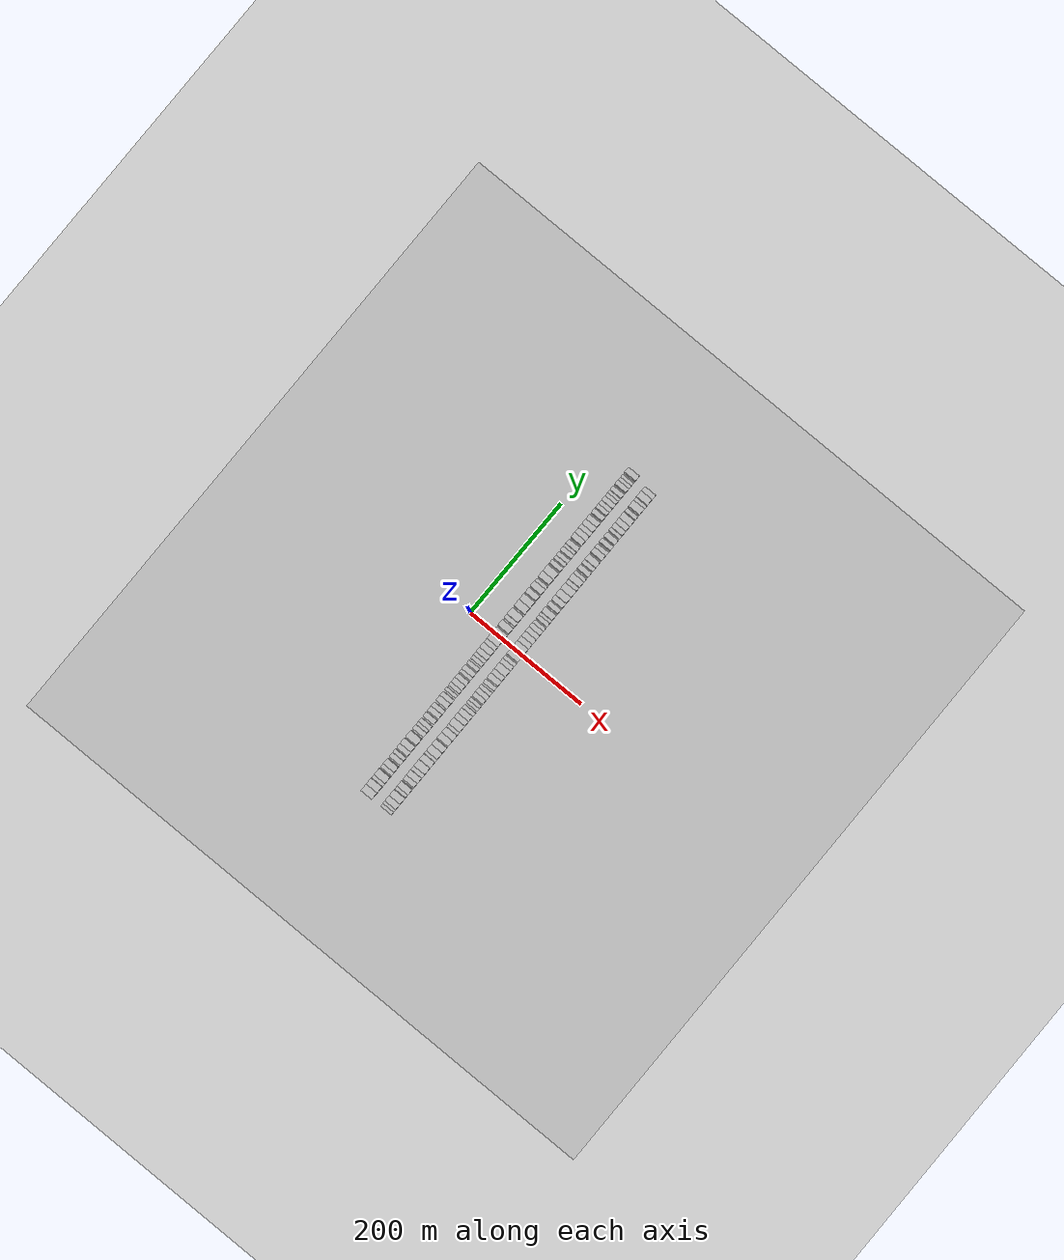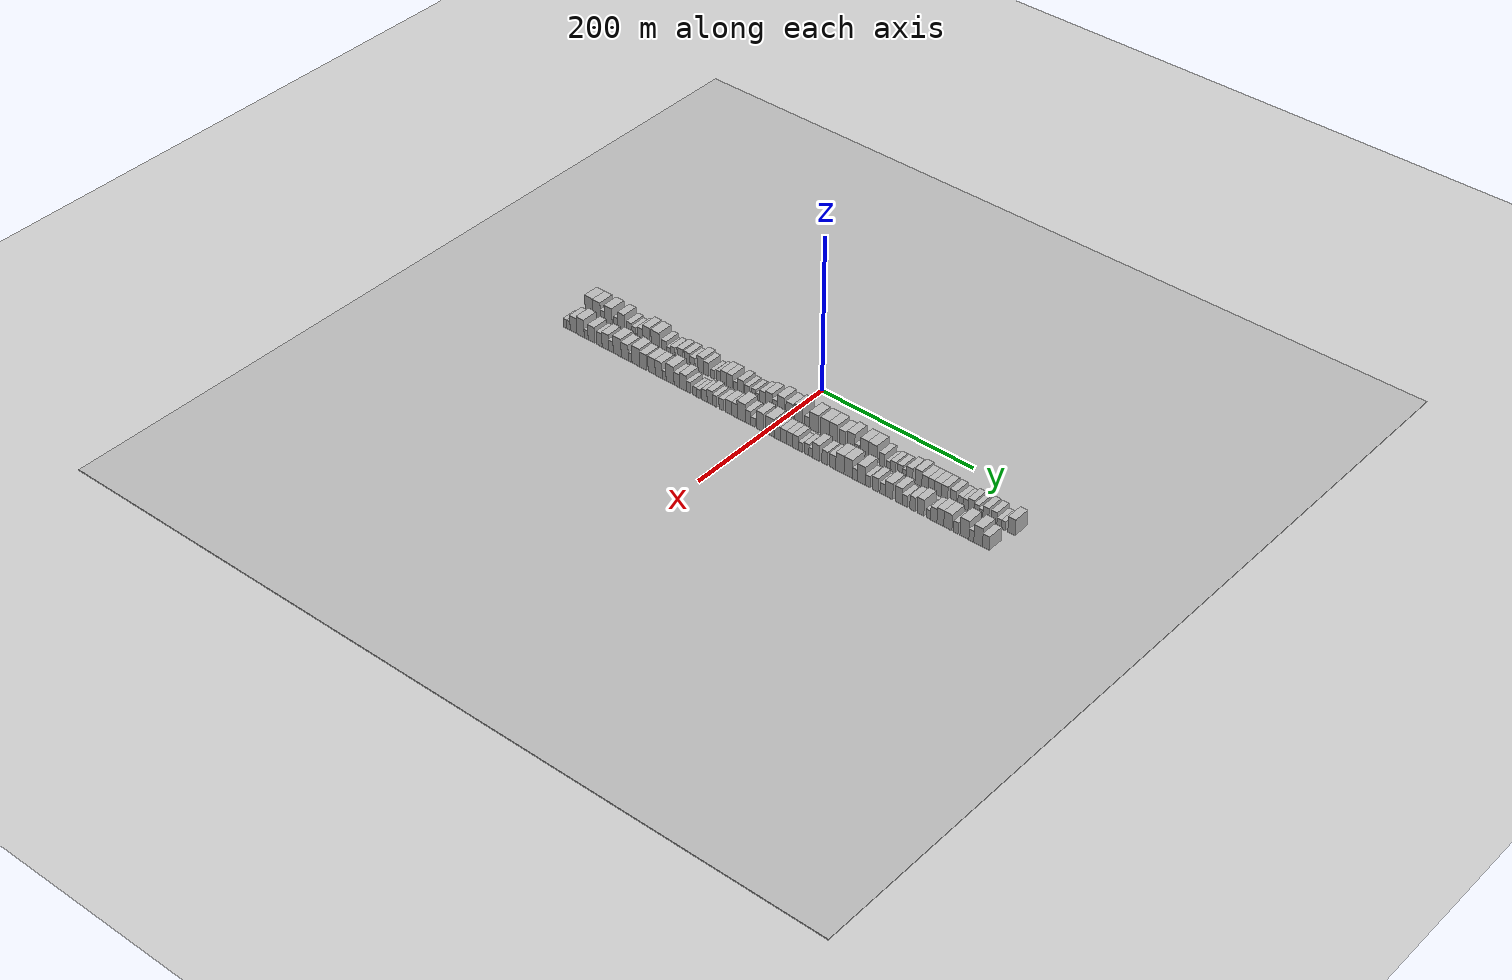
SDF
<?xml version="1.0" encoding="utf-8"?>

<sdf version="1.6">

   <world name="default">

      <gui fullscreen="0">

         <camera name="user_camera">

            <pose>-15 0 4.57585 0 0 0</pose>

            <view_controller>orbit</view_controller>

         </camera>

      </gui>

      <scene>

         <sky>

           <clouds>

             <speed>12</speed>

           </clouds>

         </sky>

         <ambient>0.4 0.4 0.4 1</ambient>

         <background>0.7 0.7 0.7 1</background>

         <shadows>1</shadows>

      </scene>

      <gravity>0 0 -9.8066</gravity>

      <magnetic_field>6e-06 2.3e-05 -4.2e-05</magnetic_field>

      <physics default="0" name="default_physics" type="ode">

         <ode>

            <solver>

               <type>quick</type>

               <iters>10</iters>

               <sor>1.0</sor>

               <use_dynamic_moi_rescaling>0</use_dynamic_moi_rescaling>

            </solver>

            <constraints>

               <cfm>0</cfm>

               <erp>0.2</erp>

               <contact_max_correcting_vel>100</contact_max_correcting_vel>

               <contact_surface_layer>0.001</contact_surface_layer>

            </constraints>

         </ode>

         <max_step_size>0.004</max_step_size>

         <real_time_factor>1</real_time_factor>

         <real_time_update_rate>250</real_time_update_rate>

      </physics>

      <light name="sun" type="directional">

         <cast_shadows>1</cast_shadows>

         <pose>0 0 10 0 0 0</pose>

         <diffuse>0.8 0.8 0.8 1</diffuse>

         <specular>0.2 0.2 0.2 1</specular>

         <attenuation>

            <range>1000</range>

            <constant>0.9</constant>

            <linear>0.01</linear>

            <quadratic>0.001</quadratic>

         </attenuation>

         <direction>-0.5 0.1 -0.9</direction>

      </light>

      <include>

         <name>ground_plane_1</name>

         <uri>model://HANNAS_ground_plane</uri>

         <pose>0 0 0  0 0 0</pose>

      </include>

      <include>

         <name>ground_plane_2</name>

         <uri>model://HANNAS_ground_plane</uri>

         <pose>100 0 0  0 0 0</pose>

      </include>

      <model name="building_1">

         <static>1</static>

         <pose frame="">50.0000 -284.0708 0 0.000000 0.000000 0.000000</pose>

         <link name="link">

            <pose frame="">0 0 12.00 0 0 0</pose>

            <collision name="collision">

               <geometry>

                  <box>

                     <size>20.0000 11.8585 24.0000</size>

                  </box>

               </geometry>

               <max_contacts>10</max_contacts>

               <surface>

                  <contact>

                     <ode/>

                  </contact>

                  <bounce/>

                  <friction>

                     <torsional>

                        <ode/>

                     </torsional>

                     <ode/>

                  </friction>

               </surface>

            </collision>

            <visual name="visual">

               <cast_shadows>0</cast_shadows>

               <geometry>

                  <box>

                     <size>20.0000 11.8585 24.0000</size>

                  </box>

               </geometry>

               <material>

                  <script>

                     <uri>model://HANNAS_wall/materials/scripts</uri>

                     <uri>model://HANNAS_wall/materials/textures</uri>

                     <name>vrc/HANNAS_wall</name>

                  </script>

               </material>

            </visual>

            <self_collide>0</self_collide>

            <enable_wind>0</enable_wind>

            <kinematic>0</kinematic>

         </link>

      </model>

      <model name="building_2">

         <static>1</static>

         <pose frame="">50.0000 -272.6437 0 0.000000 0.000000 0.000000</pose>

         <link name="link">

            <pose frame="">0 0 12.00 0 0 0</pose>

            <collision name="collision">

               <geometry>

                  <box>

                     <size>20.0000 10.9956 24.0000</size>

                  </box>

               </geometry>

               <max_contacts>10</max_contacts>

               <surface>

                  <contact>

                     <ode/>

                  </contact>

                  <bounce/>

                  <friction>

                     <torsional>

                        <ode/>

                     </torsional>

                     <ode/>

                  </friction>

               </surface>

            </collision>

            <visual name="visual">

               <cast_shadows>0</cast_shadows>

               <geometry>

                  <box>

                     <size>20.0000 10.9956 24.0000</size>

                  </box>

               </geometry>

               <material>

                  <script>

                     <uri>model://HANNAS_wall/materials/scripts</uri>

                     <uri>model://HANNAS_wall/materials/textures</uri>

                     <name>vrc/HANNAS_wall</name>

                  </script>

               </material>

            </visual>

            <self_collide>0</self_collide>

            <enable_wind>0</enable_wind>

            <kinematic>0</kinematic>

         </link>

      </model>

      <model name="building_3">

         <static>1</static>

         <pose frame="">50.0000 -264.1438 0 0.000000 0.000000 0.000000</pose>

         <link name="link">

            <pose frame="">0 0 7.50 0 0 0</pose>

            <collision name="collision">

               <geometry>

                  <box>

                     <size>20.0000 6.0041 15.0000</size>

                  </box>

               </geometry>

               <max_contacts>10</max_contacts>

               <surface>

                  <contact>

                     <ode/>

                  </contact>

                  <bounce/>

                  <friction>

                     <torsional>

                        <ode/>

                     </torsional>

                     <ode/>

                  </friction>

               </surface>

            </collision>

            <visual name="visual">

               <cast_shadows>0</cast_shadows>

               <geometry>

                  <box>

                     <size>20.0000 6.0041 15.0000</size>

                  </box>

               </geometry>

               <material>

                  <script>

                     <uri>model://HANNAS_wall/materials/scripts</uri>

                     <uri>model://HANNAS_wall/materials/textures</uri>

                     <name>vrc/HANNAS_wall</name>

                  </script>

               </material>

            </visual>

            <self_collide>0</self_collide>

            <enable_wind>0</enable_wind>

            <kinematic>0</kinematic>

         </link>

      </model>

      <model name="building_4">

         <static>1</static>

         <pose frame="">50.0000 -255.4517 0 0.000000 0.000000 0.000000</pose>

         <link name="link">

            <pose frame="">0 0 12.00 0 0 0</pose>

            <collision name="collision">

               <geometry>

                  <box>

                     <size>20.0000 11.3802 24.0000</size>

                  </box>

               </geometry>

               <max_contacts>10</max_contacts>

               <surface>

                  <contact>

                     <ode/>

                  </contact>

                  <bounce/>

                  <friction>

                     <torsional>

                        <ode/>

                     </torsional>

                     <ode/>

                  </friction>

               </surface>

            </collision>

            <visual name="visual">

               <cast_shadows>0</cast_shadows>

               <geometry>

                  <box>

                     <size>20.0000 11.3802 24.0000</size>

                  </box>

               </geometry>

               <material>

                  <script>

                     <uri>model://HANNAS_wall/materials/scripts</uri>

                     <uri>model://HANNAS_wall/materials/textures</uri>

                     <name>vrc/HANNAS_wall</name>

                  </script>

               </material>

            </visual>

            <self_collide>0</self_collide>

            <enable_wind>0</enable_wind>

            <kinematic>0</kinematic>

         </link>

      </model>

      <model name="building_5">

         <static>1</static>

         <pose frame="">50.0000 -244.4778 0 0.000000 0.000000 0.000000</pose>

         <link name="link">

            <pose frame="">0 0 7.50 0 0 0</pose>

            <collision name="collision">

               <geometry>

                  <box>

                     <size>20.0000 6.5676 15.0000</size>

                  </box>

               </geometry>

               <max_contacts>10</max_contacts>

               <surface>

                  <contact>

                     <ode/>

                  </contact>

                  <bounce/>

                  <friction>

                     <torsional>

                        <ode/>

                     </torsional>

                     <ode/>

                  </friction>

               </surface>

            </collision>

            <visual name="visual">

               <cast_shadows>0</cast_shadows>

               <geometry>

                  <box>

                     <size>20.0000 6.5676 15.0000</size>

                  </box>

               </geometry>

               <material>

                  <script>

                     <uri>model://HANNAS_wall/materials/scripts</uri>

                     <uri>model://HANNAS_wall/materials/textures</uri>

                     <name>vrc/HANNAS_wall</name>

                  </script>

               </material>

            </visual>

            <self_collide>0</self_collide>

            <enable_wind>0</enable_wind>

            <kinematic>0</kinematic>

         </link>

      </model>

      <model name="building_6">

         <static>1</static>

         <pose frame="">50.0000 -236.3527 0 0.000000 0.000000 0.000000</pose>

         <link name="link">

            <pose frame="">0 0 12.00 0 0 0</pose>

            <collision name="collision">

               <geometry>

                  <box>

                     <size>20.0000 9.6825 24.0000</size>

                  </box>

               </geometry>

               <max_contacts>10</max_contacts>

               <surface>

                  <contact>

                     <ode/>

                  </contact>

                  <bounce/>

                  <friction>

                     <torsional>

                        <ode/>

                     </torsional>

                     <ode/>

                  </friction>

               </surface>

            </collision>

            <visual name="visual">

               <cast_shadows>0</cast_shadows>

               <geometry>

                  <box>

                     <size>20.0000 9.6825 24.0000</size>

                  </box>

               </geometry>

               <material>

                  <script>

                     <uri>model://HANNAS_wall/materials/scripts</uri>

                     <uri>model://HANNAS_wall/materials/textures</uri>

                     <name>vrc/HANNAS_wall</name>

                  </script>

               </material>

            </visual>

            <self_collide>0</self_collide>

            <enable_wind>0</enable_wind>

            <kinematic>0</kinematic>

         </link>

      </model>

      <model name="building_7">

         <static>1</static>

         <pose frame="">50.0000 -224.6390 0 0.000000 0.000000 0.000000</pose>

         <link name="link">

            <pose frame="">0 0 9.00 0 0 0</pose>

            <collision name="collision">

               <geometry>

                  <box>

                     <size>20.0000 7.7450 18.0000</size>

                  </box>

               </geometry>

               <max_contacts>10</max_contacts>

               <surface>

                  <contact>

                     <ode/>

                  </contact>

                  <bounce/>

                  <friction>

                     <torsional>

                        <ode/>

                     </torsional>

                     <ode/>

                  </friction>

               </surface>

            </collision>

            <visual name="visual">

               <cast_shadows>0</cast_shadows>

               <geometry>

                  <box>

                     <size>20.0000 7.7450 18.0000</size>

                  </box>

               </geometry>

               <material>

                  <script>

                     <uri>model://HANNAS_wall/materials/scripts</uri>

                     <uri>model://HANNAS_wall/materials/textures</uri>

                     <name>vrc/HANNAS_wall</name>

                  </script>

               </material>

            </visual>

            <self_collide>0</self_collide>

            <enable_wind>0</enable_wind>

            <kinematic>0</kinematic>

         </link>

      </model>

      <model name="building_8">

         <static>1</static>

         <pose frame="">50.0000 -217.6239 0 0.000000 0.000000 0.000000</pose>

         <link name="link">

            <pose frame="">0 0 7.50 0 0 0</pose>

            <collision name="collision">

               <geometry>

                  <box>

                     <size>20.0000 6.2851 15.0000</size>

                  </box>

               </geometry>

               <max_contacts>10</max_contacts>

               <surface>

                  <contact>

                     <ode/>

                  </contact>

                  <bounce/>

                  <friction>

                     <torsional>

                        <ode/>

                     </torsional>

                     <ode/>

                  </friction>

               </surface>

            </collision>

            <visual name="visual">

               <cast_shadows>0</cast_shadows>

               <geometry>

                  <box>

                     <size>20.0000 6.2851 15.0000</size>

                  </box>

               </geometry>

               <material>

                  <script>

                     <uri>model://HANNAS_wall/materials/scripts</uri>

                     <uri>model://HANNAS_wall/materials/textures</uri>

                     <name>vrc/HANNAS_wall</name>

                  </script>

               </material>

            </visual>

            <self_collide>0</self_collide>

            <enable_wind>0</enable_wind>

            <kinematic>0</kinematic>

         </link>

      </model>

      <model name="building_9">

         <static>1</static>

         <pose frame="">50.0000 -208.3122 0 0.000000 0.000000 0.000000</pose>

         <link name="link">

            <pose frame="">0 0 9.00 0 0 0</pose>

            <collision name="collision">

               <geometry>

                  <box>

                     <size>20.0000 8.3385 18.0000</size>

                  </box>

               </geometry>

               <max_contacts>10</max_contacts>

               <surface>

                  <contact>

                     <ode/>

                  </contact>

                  <bounce/>

                  <friction>

                     <torsional>

                        <ode/>

                     </torsional>

                     <ode/>

                  </friction>

               </surface>

            </collision>

            <visual name="visual">

               <cast_shadows>0</cast_shadows>

               <geometry>

                  <box>

                     <size>20.0000 8.3385 18.0000</size>

                  </box>

               </geometry>

               <material>

                  <script>

                     <uri>model://HANNAS_wall/materials/scripts</uri>

                     <uri>model://HANNAS_wall/materials/textures</uri>

                     <name>vrc/HANNAS_wall</name>

                  </script>

               </material>

            </visual>

            <self_collide>0</self_collide>

            <enable_wind>0</enable_wind>

            <kinematic>0</kinematic>

         </link>

      </model>

      <model name="building_10">

         <static>1</static>

         <pose frame="">50.0000 -199.2481 0 0.000000 0.000000 0.000000</pose>

         <link name="link">

            <pose frame="">0 0 12.00 0 0 0</pose>

            <collision name="collision">

               <geometry>

                  <box>

                     <size>20.0000 9.7897 24.0000</size>

                  </box>

               </geometry>

               <max_contacts>10</max_contacts>

               <surface>

                  <contact>

                     <ode/>

                  </contact>

                  <bounce/>

                  <friction>

                     <torsional>

                        <ode/>

                     </torsional>

                     <ode/>

                  </friction>

               </surface>

            </collision>

            <visual name="visual">

               <cast_shadows>0</cast_shadows>

               <geometry>

                  <box>

                     <size>20.0000 9.7897 24.0000</size>

                  </box>

               </geometry>

               <material>

                  <script>

                     <uri>model://HANNAS_wall/materials/scripts</uri>

                     <uri>model://HANNAS_wall/materials/textures</uri>

                     <name>vrc/HANNAS_wall</name>

                  </script>

               </material>

            </visual>

            <self_collide>0</self_collide>

            <enable_wind>0</enable_wind>

            <kinematic>0</kinematic>

         </link>

      </model>

      <model name="building_11">

         <static>1</static>

         <pose frame="">50.0000 -186.4286 0 0.000000 0.000000 0.000000</pose>

         <link name="link">

            <pose frame="">0 0 12.00 0 0 0</pose>

            <collision name="collision">

               <geometry>

                  <box>

                     <size>20.0000 11.8492 24.0000</size>

                  </box>

               </geometry>

               <max_contacts>10</max_contacts>

               <surface>

                  <contact>

                     <ode/>

                  </contact>

                  <bounce/>

                  <friction>

                     <torsional>

                        <ode/>

                     </torsional>

                     <ode/>

                  </friction>

               </surface>

            </collision>

            <visual name="visual">

               <cast_shadows>0</cast_shadows>

               <geometry>

                  <box>

                     <size>20.0000 11.8492 24.0000</size>

                  </box>

               </geometry>

               <material>

                  <script>

                     <uri>model://HANNAS_wall/materials/scripts</uri>

                     <uri>model://HANNAS_wall/materials/textures</uri>

                     <name>vrc/HANNAS_wall</name>

                  </script>

               </material>

            </visual>

            <self_collide>0</self_collide>

            <enable_wind>0</enable_wind>

            <kinematic>0</kinematic>

         </link>

      </model>

      <model name="building_12">

         <static>1</static>

         <pose frame="">50.0000 -173.7091 0 0.000000 0.000000 0.000000</pose>

         <link name="link">

            <pose frame="">0 0 9.00 0 0 0</pose>

            <collision name="collision">

               <geometry>

                  <box>

                     <size>20.0000 7.5898 18.0000</size>

                  </box>

               </geometry>

               <max_contacts>10</max_contacts>

               <surface>

                  <contact>

                     <ode/>

                  </contact>

                  <bounce/>

                  <friction>

                     <torsional>

                        <ode/>

                     </torsional>

                     <ode/>

                  </friction>

               </surface>

            </collision>

            <visual name="visual">

               <cast_shadows>0</cast_shadows>

               <geometry>

                  <box>

                     <size>20.0000 7.5898 18.0000</size>

                  </box>

               </geometry>

               <material>

                  <script>

                     <uri>model://HANNAS_wall/materials/scripts</uri>

                     <uri>model://HANNAS_wall/materials/textures</uri>

                     <name>vrc/HANNAS_wall</name>

                  </script>

               </material>

            </visual>

            <self_collide>0</self_collide>

            <enable_wind>0</enable_wind>

            <kinematic>0</kinematic>

         </link>

      </model>

      <model name="building_13">

         <static>1</static>

         <pose frame="">50.0000 -167.3021 0 0.000000 0.000000 0.000000</pose>

         <link name="link">

            <pose frame="">0 0 6.00 0 0 0</pose>

            <collision name="collision">

               <geometry>

                  <box>

                     <size>20.0000 5.2240 12.0000</size>

                  </box>

               </geometry>

               <max_contacts>10</max_contacts>

               <surface>

                  <contact>

                     <ode/>

                  </contact>

                  <bounce/>

                  <friction>

                     <torsional>

                        <ode/>

                     </torsional>

                     <ode/>

                  </friction>

               </surface>

            </collision>

            <visual name="visual">

               <cast_shadows>0</cast_shadows>

               <geometry>

                  <box>

                     <size>20.0000 5.2240 12.0000</size>

                  </box>

               </geometry>

               <material>

                  <script>

                     <uri>model://HANNAS_wall/materials/scripts</uri>

                     <uri>model://HANNAS_wall/materials/textures</uri>

                     <name>vrc/HANNAS_wall</name>

                  </script>

               </material>

            </visual>

            <self_collide>0</self_collide>

            <enable_wind>0</enable_wind>

            <kinematic>0</kinematic>

         </link>

      </model>

      <model name="building_14">

         <static>1</static>

         <pose frame="">50.0000 -161.2082 0 0.000000 0.000000 0.000000</pose>

         <link name="link">

            <pose frame="">0 0 7.50 0 0 0</pose>

            <collision name="collision">

               <geometry>

                  <box>

                     <size>20.0000 6.9639 15.0000</size>

                  </box>

               </geometry>

               <max_contacts>10</max_contacts>

               <surface>

                  <contact>

                     <ode/>

                  </contact>

                  <bounce/>

                  <friction>

                     <torsional>

                        <ode/>

                     </torsional>

                     <ode/>

                  </friction>

               </surface>

            </collision>

            <visual name="visual">

               <cast_shadows>0</cast_shadows>

               <geometry>

                  <box>

                     <size>20.0000 6.9639 15.0000</size>

                  </box>

               </geometry>

               <material>

                  <script>

                     <uri>model://HANNAS_wall/materials/scripts</uri>

                     <uri>model://HANNAS_wall/materials/textures</uri>

                     <name>vrc/HANNAS_wall</name>

                  </script>

               </material>

            </visual>

            <self_collide>0</self_collide>

            <enable_wind>0</enable_wind>

            <kinematic>0</kinematic>

         </link>

      </model>

      <model name="building_15">

         <static>1</static>

         <pose frame="">50.0000 -150.6885 0 0.000000 0.000000 0.000000</pose>

         <link name="link">

            <pose frame="">0 0 9.00 0 0 0</pose>

            <collision name="collision">

               <geometry>

                  <box>

                     <size>20.0000 8.0754 18.0000</size>

                  </box>

               </geometry>

               <max_contacts>10</max_contacts>

               <surface>

                  <contact>

                     <ode/>

                  </contact>

                  <bounce/>

                  <friction>

                     <torsional>

                        <ode/>

                     </torsional>

                     <ode/>

                  </friction>

               </surface>

            </collision>

            <visual name="visual">

               <cast_shadows>0</cast_shadows>

               <geometry>

                  <box>

                     <size>20.0000 8.0754 18.0000</size>

                  </box>

               </geometry>

               <material>

                  <script>

                     <uri>model://HANNAS_wall/materials/scripts</uri>

                     <uri>model://HANNAS_wall/materials/textures</uri>

                     <name>vrc/HANNAS_wall</name>

                  </script>

               </material>

            </visual>

            <self_collide>0</self_collide>

            <enable_wind>0</enable_wind>

            <kinematic>0</kinematic>

         </link>

      </model>

      <model name="building_16">

         <static>1</static>

         <pose frame="">50.0000 -140.4494 0 0.000000 0.000000 0.000000</pose>

         <link name="link">

            <pose frame="">0 0 9.00 0 0 0</pose>

            <collision name="collision">

               <geometry>

                  <box>

                     <size>20.0000 8.4030 18.0000</size>

                  </box>

               </geometry>

               <max_contacts>10</max_contacts>

               <surface>

                  <contact>

                     <ode/>

                  </contact>

                  <bounce/>

                  <friction>

                     <torsional>

                        <ode/>

                     </torsional>

                     <ode/>

                  </friction>

               </surface>

            </collision>

            <visual name="visual">

               <cast_shadows>0</cast_shadows>

               <geometry>

                  <box>

                     <size>20.0000 8.4030 18.0000</size>

                  </box>

               </geometry>

               <material>

                  <script>

                     <uri>model://HANNAS_wall/materials/scripts</uri>

                     <uri>model://HANNAS_wall/materials/textures</uri>

                     <name>vrc/HANNAS_wall</name>

                  </script>

               </material>

            </visual>

            <self_collide>0</self_collide>

            <enable_wind>0</enable_wind>

            <kinematic>0</kinematic>

         </link>

      </model>

      <model name="building_17">

         <static>1</static>

         <pose frame="">50.0000 -132.6413 0 0.000000 0.000000 0.000000</pose>

         <link name="link">

            <pose frame="">0 0 7.50 0 0 0</pose>

            <collision name="collision">

               <geometry>

                  <box>

                     <size>20.0000 7.2131 15.0000</size>

                  </box>

               </geometry>

               <max_contacts>10</max_contacts>

               <surface>

                  <contact>

                     <ode/>

                  </contact>

                  <bounce/>

                  <friction>

                     <torsional>

                        <ode/>

                     </torsional>

                     <ode/>

                  </friction>

               </surface>

            </collision>

            <visual name="visual">

               <cast_shadows>0</cast_shadows>

               <geometry>

                  <box>

                     <size>20.0000 7.2131 15.0000</size>

                  </box>

               </geometry>

               <material>

                  <script>

                     <uri>model://HANNAS_wall/materials/scripts</uri>

                     <uri>model://HANNAS_wall/materials/textures</uri>

                     <name>vrc/HANNAS_wall</name>

                  </script>

               </material>

            </visual>

            <self_collide>0</self_collide>

            <enable_wind>0</enable_wind>

            <kinematic>0</kinematic>

         </link>

      </model>

      <model name="building_18">

         <static>1</static>

         <pose frame="">50.0000 -121.4385 0 0.000000 0.000000 0.000000</pose>

         <link name="link">

            <pose frame="">0 0 10.50 0 0 0</pose>

            <collision name="collision">

               <geometry>

                  <box>

                     <size>20.0000 9.1925 21.0000</size>

                  </box>

               </geometry>

               <max_contacts>10</max_contacts>

               <surface>

                  <contact>

                     <ode/>

                  </contact>

                  <bounce/>

                  <friction>

                     <torsional>

                        <ode/>

                     </torsional>

                     <ode/>

                  </friction>

               </surface>

            </collision>

            <visual name="visual">

               <cast_shadows>0</cast_shadows>

               <geometry>

                  <box>

                     <size>20.0000 9.1925 21.0000</size>

                  </box>

               </geometry>

               <material>

                  <script>

                     <uri>model://HANNAS_wall/materials/scripts</uri>

                     <uri>model://HANNAS_wall/materials/textures</uri>

                     <name>vrc/HANNAS_wall</name>

                  </script>

               </material>

            </visual>

            <self_collide>0</self_collide>

            <enable_wind>0</enable_wind>

            <kinematic>0</kinematic>

         </link>

      </model>

      <model name="building_19">

         <static>1</static>

         <pose frame="">50.0000 -113.2091 0 0.000000 0.000000 0.000000</pose>

         <link name="link">

            <pose frame="">0 0 9.00 0 0 0</pose>

            <collision name="collision">

               <geometry>

                  <box>

                     <size>20.0000 7.2663 18.0000</size>

                  </box>

               </geometry>

               <max_contacts>10</max_contacts>

               <surface>

                  <contact>

                     <ode/>

                  </contact>

                  <bounce/>

                  <friction>

                     <torsional>

                        <ode/>

                     </torsional>

                     <ode/>

                  </friction>

               </surface>

            </collision>

            <visual name="visual">

               <cast_shadows>0</cast_shadows>

               <geometry>

                  <box>

                     <size>20.0000 7.2663 18.0000</size>

                  </box>

               </geometry>

               <material>

                  <script>

                     <uri>model://HANNAS_wall/materials/scripts</uri>

                     <uri>model://HANNAS_wall/materials/textures</uri>

                     <name>vrc/HANNAS_wall</name>

                  </script>

               </material>

            </visual>

            <self_collide>0</self_collide>

            <enable_wind>0</enable_wind>

            <kinematic>0</kinematic>

         </link>

      </model>

      <model name="building_20">

         <static>1</static>

         <pose frame="">50.0000 -104.0275 0 0.000000 0.000000 0.000000</pose>

         <link name="link">

            <pose frame="">0 0 6.00 0 0 0</pose>

            <collision name="collision">

               <geometry>

                  <box>

                     <size>20.0000 5.0969 12.0000</size>

                  </box>

               </geometry>

               <max_contacts>10</max_contacts>

               <surface>

                  <contact>

                     <ode/>

                  </contact>

                  <bounce/>

                  <friction>

                     <torsional>

                        <ode/>

                     </torsional>

                     <ode/>

                  </friction>

               </surface>

            </collision>

            <visual name="visual">

               <cast_shadows>0</cast_shadows>

               <geometry>

                  <box>

                     <size>20.0000 5.0969 12.0000</size>

                  </box>

               </geometry>

               <material>

                  <script>

                     <uri>model://HANNAS_wall/materials/scripts</uri>

                     <uri>model://HANNAS_wall/materials/textures</uri>

                     <name>vrc/HANNAS_wall</name>

                  </script>

               </material>

            </visual>

            <self_collide>0</self_collide>

            <enable_wind>0</enable_wind>

            <kinematic>0</kinematic>

         </link>

      </model>

      <model name="building_21">

         <static>1</static>

         <pose frame="">50.0000 -95.4334 0 0.000000 0.000000 0.000000</pose>

         <link name="link">

            <pose frame="">0 0 7.50 0 0 0</pose>

            <collision name="collision">

               <geometry>

                  <box>

                     <size>20.0000 6.0914 15.0000</size>

                  </box>

               </geometry>

               <max_contacts>10</max_contacts>

               <surface>

                  <contact>

                     <ode/>

                  </contact>

                  <bounce/>

                  <friction>

                     <torsional>

                        <ode/>

                     </torsional>

                     <ode/>

                  </friction>

               </surface>

            </collision>

            <visual name="visual">

               <cast_shadows>0</cast_shadows>

               <geometry>

                  <box>

                     <size>20.0000 6.0914 15.0000</size>

                  </box>

               </geometry>

               <material>

                  <script>

                     <uri>model://HANNAS_wall/materials/scripts</uri>

                     <uri>model://HANNAS_wall/materials/textures</uri>

                     <name>vrc/HANNAS_wall</name>

                  </script>

               </material>

            </visual>

            <self_collide>0</self_collide>

            <enable_wind>0</enable_wind>

            <kinematic>0</kinematic>

         </link>

      </model>

      <model name="building_22">

         <static>1</static>

         <pose frame="">50.0000 -88.2341 0 0.000000 0.000000 0.000000</pose>

         <link name="link">

            <pose frame="">0 0 9.00 0 0 0</pose>

            <collision name="collision">

               <geometry>

                  <box>

                     <size>20.0000 8.3072 18.0000</size>

                  </box>

               </geometry>

               <max_contacts>10</max_contacts>

               <surface>

                  <contact>

                     <ode/>

                  </contact>

                  <bounce/>

                  <friction>

                     <torsional>

                        <ode/>

                     </torsional>

                     <ode/>

                  </friction>

               </surface>

            </collision>

            <visual name="visual">

               <cast_shadows>0</cast_shadows>

               <geometry>

                  <box>

                     <size>20.0000 8.3072 18.0000</size>

                  </box>

               </geometry>

               <material>

                  <script>

                     <uri>model://HANNAS_wall/materials/scripts</uri>

                     <uri>model://HANNAS_wall/materials/textures</uri>

                     <name>vrc/HANNAS_wall</name>

                  </script>

               </material>

            </visual>

            <self_collide>0</self_collide>

            <enable_wind>0</enable_wind>

            <kinematic>0</kinematic>

         </link>

      </model>

      <model name="building_23">

         <static>1</static>

         <pose frame="">50.0000 -80.2416 0 0.000000 0.000000 0.000000</pose>

         <link name="link">

            <pose frame="">0 0 9.00 0 0 0</pose>

            <collision name="collision">

               <geometry>

                  <box>

                     <size>20.0000 7.6779 18.0000</size>

                  </box>

               </geometry>

               <max_contacts>10</max_contacts>

               <surface>

                  <contact>

                     <ode/>

                  </contact>

                  <bounce/>

                  <friction>

                     <torsional>

                        <ode/>

                     </torsional>

                     <ode/>

                  </friction>

               </surface>

            </collision>

            <visual name="visual">

               <cast_shadows>0</cast_shadows>

               <geometry>

                  <box>

                     <size>20.0000 7.6779 18.0000</size>

                  </box>

               </geometry>

               <material>

                  <script>

                     <uri>model://HANNAS_wall/materials/scripts</uri>

                     <uri>model://HANNAS_wall/materials/textures</uri>

                     <name>vrc/HANNAS_wall</name>

                  </script>

               </material>

            </visual>

            <self_collide>0</self_collide>

            <enable_wind>0</enable_wind>

            <kinematic>0</kinematic>

         </link>

      </model>

      <model name="building_24">

         <static>1</static>

         <pose frame="">50.0000 -71.5768 0 0.000000 0.000000 0.000000</pose>

         <link name="link">

            <pose frame="">0 0 6.00 0 0 0</pose>

            <collision name="collision">

               <geometry>

                  <box>

                     <size>20.0000 5.6516 12.0000</size>

                  </box>

               </geometry>

               <max_contacts>10</max_contacts>

               <surface>

                  <contact>

                     <ode/>

                  </contact>

                  <bounce/>

                  <friction>

                     <torsional>

                        <ode/>

                     </torsional>

                     <ode/>

                  </friction>

               </surface>

            </collision>

            <visual name="visual">

               <cast_shadows>0</cast_shadows>

               <geometry>

                  <box>

                     <size>20.0000 5.6516 12.0000</size>

                  </box>

               </geometry>

               <material>

                  <script>

                     <uri>model://HANNAS_wall/materials/scripts</uri>

                     <uri>model://HANNAS_wall/materials/textures</uri>

                     <name>vrc/HANNAS_wall</name>

                  </script>

               </material>

            </visual>

            <self_collide>0</self_collide>

            <enable_wind>0</enable_wind>

            <kinematic>0</kinematic>

         </link>

      </model>

      <model name="building_25">

         <static>1</static>

         <pose frame="">50.0000 -64.7696 0 0.000000 0.000000 0.000000</pose>

         <link name="link">

            <pose frame="">0 0 9.00 0 0 0</pose>

            <collision name="collision">

               <geometry>

                  <box>

                     <size>20.0000 7.9629 18.0000</size>

                  </box>

               </geometry>

               <max_contacts>10</max_contacts>

               <surface>

                  <contact>

                     <ode/>

                  </contact>

                  <bounce/>

                  <friction>

                     <torsional>

                        <ode/>

                     </torsional>

                     <ode/>

                  </friction>

               </surface>

            </collision>

            <visual name="visual">

               <cast_shadows>0</cast_shadows>

               <geometry>

                  <box>

                     <size>20.0000 7.9629 18.0000</size>

                  </box>

               </geometry>

               <material>

                  <script>

                     <uri>model://HANNAS_wall/materials/scripts</uri>

                     <uri>model://HANNAS_wall/materials/textures</uri>

                     <name>vrc/HANNAS_wall</name>

                  </script>

               </material>

            </visual>

            <self_collide>0</self_collide>

            <enable_wind>0</enable_wind>

            <kinematic>0</kinematic>

         </link>

      </model>

      <model name="building_26">

         <static>1</static>

         <pose frame="">50.0000 -55.6162 0 0.000000 0.000000 0.000000</pose>

         <link name="link">

            <pose frame="">0 0 7.50 0 0 0</pose>

            <collision name="collision">

               <geometry>

                  <box>

                     <size>20.0000 6.3438 15.0000</size>

                  </box>

               </geometry>

               <max_contacts>10</max_contacts>

               <surface>

                  <contact>

                     <ode/>

                  </contact>

                  <bounce/>

                  <friction>

                     <torsional>

                        <ode/>

                     </torsional>

                     <ode/>

                  </friction>

               </surface>

            </collision>

            <visual name="visual">

               <cast_shadows>0</cast_shadows>

               <geometry>

                  <box>

                     <size>20.0000 6.3438 15.0000</size>

                  </box>

               </geometry>

               <material>

                  <script>

                     <uri>model://HANNAS_wall/materials/scripts</uri>

                     <uri>model://HANNAS_wall/materials/textures</uri>

                     <name>vrc/HANNAS_wall</name>

                  </script>

               </material>

            </visual>

            <self_collide>0</self_collide>

            <enable_wind>0</enable_wind>

            <kinematic>0</kinematic>

         </link>

      </model>

      <model name="building_27">

         <static>1</static>

         <pose frame="">50.0000 -46.2891 0 0.000000 0.000000 0.000000</pose>

         <link name="link">

            <pose frame="">0 0 7.50 0 0 0</pose>

            <collision name="collision">

               <geometry>

                  <box>

                     <size>20.0000 6.3104 15.0000</size>

                  </box>

               </geometry>

               <max_contacts>10</max_contacts>

               <surface>

                  <contact>

                     <ode/>

                  </contact>

                  <bounce/>

                  <friction>

                     <torsional>

                        <ode/>

                     </torsional>

                     <ode/>

                  </friction>

               </surface>

            </collision>

            <visual name="visual">

               <cast_shadows>0</cast_shadows>

               <geometry>

                  <box>

                     <size>20.0000 6.3104 15.0000</size>

                  </box>

               </geometry>

               <material>

                  <script>

                     <uri>model://HANNAS_wall/materials/scripts</uri>

                     <uri>model://HANNAS_wall/materials/textures</uri>

                     <name>vrc/HANNAS_wall</name>

                  </script>

               </material>

            </visual>

            <self_collide>0</self_collide>

            <enable_wind>0</enable_wind>

            <kinematic>0</kinematic>

         </link>

      </model>

      <model name="building_28">

         <static>1</static>

         <pose frame="">50.0000 -40.4163 0 0.000000 0.000000 0.000000</pose>

         <link name="link">

            <pose frame="">0 0 6.00 0 0 0</pose>

            <collision name="collision">

               <geometry>

                  <box>

                     <size>20.0000 5.4352 12.0000</size>

                  </box>

               </geometry>

               <max_contacts>10</max_contacts>

               <surface>

                  <contact>

                     <ode/>

                  </contact>

                  <bounce/>

                  <friction>

                     <torsional>

                        <ode/>

                     </torsional>

                     <ode/>

                  </friction>

               </surface>

            </collision>

            <visual name="visual">

               <cast_shadows>0</cast_shadows>

               <geometry>

                  <box>

                     <size>20.0000 5.4352 12.0000</size>

                  </box>

               </geometry>

               <material>

                  <script>

                     <uri>model://HANNAS_wall/materials/scripts</uri>

                     <uri>model://HANNAS_wall/materials/textures</uri>

                     <name>vrc/HANNAS_wall</name>

                  </script>

               </material>

            </visual>

            <self_collide>0</self_collide>

            <enable_wind>0</enable_wind>

            <kinematic>0</kinematic>

         </link>

      </model>

      <model name="building_29">

         <static>1</static>

         <pose frame="">50.0000 -33.6156 0 0.000000 0.000000 0.000000</pose>

         <link name="link">

            <pose frame="">0 0 9.00 0 0 0</pose>

            <collision name="collision">

               <geometry>

                  <box>

                     <size>20.0000 8.1662 18.0000</size>

                  </box>

               </geometry>

               <max_contacts>10</max_contacts>

               <surface>

                  <contact>

                     <ode/>

                  </contact>

                  <bounce/>

                  <friction>

                     <torsional>

                        <ode/>

                     </torsional>

                     <ode/>

                  </friction>

               </surface>

            </collision>

            <visual name="visual">

               <cast_shadows>0</cast_shadows>

               <geometry>

                  <box>

                     <size>20.0000 8.1662 18.0000</size>

                  </box>

               </geometry>

               <material>

                  <script>

                     <uri>model://HANNAS_wall/materials/scripts</uri>

                     <uri>model://HANNAS_wall/materials/textures</uri>

                     <name>vrc/HANNAS_wall</name>

                  </script>

               </material>

            </visual>

            <self_collide>0</self_collide>

            <enable_wind>0</enable_wind>

            <kinematic>0</kinematic>

         </link>

      </model>

      <model name="building_30">

         <static>1</static>

         <pose frame="">50.0000 -24.9792 0 0.000000 0.000000 0.000000</pose>

         <link name="link">

            <pose frame="">0 0 10.50 0 0 0</pose>

            <collision name="collision">

               <geometry>

                  <box>

                     <size>20.0000 9.1068 21.0000</size>

                  </box>

               </geometry>

               <max_contacts>10</max_contacts>

               <surface>

                  <contact>

                     <ode/>

                  </contact>

                  <bounce/>

                  <friction>

                     <torsional>

                        <ode/>

                     </torsional>

                     <ode/>

                  </friction>

               </surface>

            </collision>

            <visual name="visual">

               <cast_shadows>0</cast_shadows>

               <geometry>

                  <box>

                     <size>20.0000 9.1068 21.0000</size>

                  </box>

               </geometry>

               <material>

                  <script>

                     <uri>model://HANNAS_wall/materials/scripts</uri>

                     <uri>model://HANNAS_wall/materials/textures</uri>

                     <name>vrc/HANNAS_wall</name>

                  </script>

               </material>

            </visual>

            <self_collide>0</self_collide>

            <enable_wind>0</enable_wind>

            <kinematic>0</kinematic>

         </link>

      </model>

      <model name="building_31">

         <static>1</static>

         <pose frame="">50.0000 -16.9064 0 0.000000 0.000000 0.000000</pose>

         <link name="link">

            <pose frame="">0 0 7.50 0 0 0</pose>

            <collision name="collision">

               <geometry>

                  <box>

                     <size>20.0000 7.0388 15.0000</size>

                  </box>

               </geometry>

               <max_contacts>10</max_contacts>

               <surface>

                  <contact>

                     <ode/>

                  </contact>

                  <bounce/>

                  <friction>

                     <torsional>

                        <ode/>

                     </torsional>

                     <ode/>

                  </friction>

               </surface>

            </collision>

            <visual name="visual">

               <cast_shadows>0</cast_shadows>

               <geometry>

                  <box>

                     <size>20.0000 7.0388 15.0000</size>

                  </box>

               </geometry>

               <material>

                  <script>

                     <uri>model://HANNAS_wall/materials/scripts</uri>

                     <uri>model://HANNAS_wall/materials/textures</uri>

                     <name>vrc/HANNAS_wall</name>

                  </script>

               </material>

            </visual>

            <self_collide>0</self_collide>

            <enable_wind>0</enable_wind>

            <kinematic>0</kinematic>

         </link>

      </model>

      <model name="building_32">

         <static>1</static>

         <pose frame="">50.0000 -8.5030 0 0.000000 0.000000 0.000000</pose>

         <link name="link">

            <pose frame="">0 0 12.00 0 0 0</pose>

            <collision name="collision">

               <geometry>

                  <box>

                     <size>20.0000 9.7680 24.0000</size>

                  </box>

               </geometry>

               <max_contacts>10</max_contacts>

               <surface>

                  <contact>

                     <ode/>

                  </contact>

                  <bounce/>

                  <friction>

                     <torsional>

                        <ode/>

                     </torsional>

                     <ode/>

                  </friction>

               </surface>

            </collision>

            <visual name="visual">

               <cast_shadows>0</cast_shadows>

               <geometry>

                  <box>

                     <size>20.0000 9.7680 24.0000</size>

                  </box>

               </geometry>

               <material>

                  <script>

                     <uri>model://HANNAS_wall/materials/scripts</uri>

                     <uri>model://HANNAS_wall/materials/textures</uri>

                     <name>vrc/HANNAS_wall</name>

                  </script>

               </material>

            </visual>

            <self_collide>0</self_collide>

            <enable_wind>0</enable_wind>

            <kinematic>0</kinematic>

         </link>

      </model>

      <model name="building_33">

         <static>1</static>

         <pose frame="">50.0000 3.3126 0 0.000000 0.000000 0.000000</pose>

         <link name="link">

            <pose frame="">0 0 10.50 0 0 0</pose>

            <collision name="collision">

               <geometry>

                  <box>

                     <size>20.0000 9.8631 21.0000</size>

                  </box>

               </geometry>

               <max_contacts>10</max_contacts>

               <surface>

                  <contact>

                     <ode/>

                  </contact>

                  <bounce/>

                  <friction>

                     <torsional>

                        <ode/>

                     </torsional>

                     <ode/>

                  </friction>

               </surface>

            </collision>

            <visual name="visual">

               <cast_shadows>0</cast_shadows>

               <geometry>

                  <box>

                     <size>20.0000 9.8631 21.0000</size>

                  </box>

               </geometry>

               <material>

                  <script>

                     <uri>model://HANNAS_wall/materials/scripts</uri>

                     <uri>model://HANNAS_wall/materials/textures</uri>

                     <name>vrc/HANNAS_wall</name>

                  </script>

               </material>

            </visual>

            <self_collide>0</self_collide>

            <enable_wind>0</enable_wind>

            <kinematic>0</kinematic>

         </link>

      </model>

      <model name="building_34">

         <static>1</static>

         <pose frame="">50.0000 15.6161 0 0.000000 0.000000 0.000000</pose>

         <link name="link">

            <pose frame="">0 0 12.00 0 0 0</pose>

            <collision name="collision">

               <geometry>

                  <box>

                     <size>20.0000 10.7440 24.0000</size>

                  </box>

               </geometry>

               <max_contacts>10</max_contacts>

               <surface>

                  <contact>

                     <ode/>

                  </contact>

                  <bounce/>

                  <friction>

                     <torsional>

                        <ode/>

                     </torsional>

                     <ode/>

                  </friction>

               </surface>

            </collision>

            <visual name="visual">

               <cast_shadows>0</cast_shadows>

               <geometry>

                  <box>

                     <size>20.0000 10.7440 24.0000</size>

                  </box>

               </geometry>

               <material>

                  <script>

                     <uri>model://HANNAS_wall/materials/scripts</uri>

                     <uri>model://HANNAS_wall/materials/textures</uri>

                     <name>vrc/HANNAS_wall</name>

                  </script>

               </material>

            </visual>

            <self_collide>0</self_collide>

            <enable_wind>0</enable_wind>

            <kinematic>0</kinematic>

         </link>

      </model>

      <model name="building_35">

         <static>1</static>

         <pose frame="">50.0000 27.4346 0 0.000000 0.000000 0.000000</pose>

         <link name="link">

            <pose frame="">0 0 7.50 0 0 0</pose>

            <collision name="collision">

               <geometry>

                  <box>

                     <size>20.0000 6.8929 15.0000</size>

                  </box>

               </geometry>

               <max_contacts>10</max_contacts>

               <surface>

                  <contact>

                     <ode/>

                  </contact>

                  <bounce/>

                  <friction>

                     <torsional>

                        <ode/>

                     </torsional>

                     <ode/>

                  </friction>

               </surface>

            </collision>

            <visual name="visual">

               <cast_shadows>0</cast_shadows>

               <geometry>

                  <box>

                     <size>20.0000 6.8929 15.0000</size>

                  </box>

               </geometry>

               <material>

                  <script>

                     <uri>model://HANNAS_wall/materials/scripts</uri>

                     <uri>model://HANNAS_wall/materials/textures</uri>

                     <name>vrc/HANNAS_wall</name>

                  </script>

               </material>

            </visual>

            <self_collide>0</self_collide>

            <enable_wind>0</enable_wind>

            <kinematic>0</kinematic>

         </link>

      </model>

      <model name="building_36">

         <static>1</static>

         <pose frame="">50.0000 36.8483 0 0.000000 0.000000 0.000000</pose>

         <link name="link">

            <pose frame="">0 0 12.00 0 0 0</pose>

            <collision name="collision">

               <geometry>

                  <box>

                     <size>20.0000 11.9345 24.0000</size>

                  </box>

               </geometry>

               <max_contacts>10</max_contacts>

               <surface>

                  <contact>

                     <ode/>

                  </contact>

                  <bounce/>

                  <friction>

                     <torsional>

                        <ode/>

                     </torsional>

                     <ode/>

                  </friction>

               </surface>

            </collision>

            <visual name="visual">

               <cast_shadows>0</cast_shadows>

               <geometry>

                  <box>

                     <size>20.0000 11.9345 24.0000</size>

                  </box>

               </geometry>

               <material>

                  <script>

                     <uri>model://HANNAS_wall/materials/scripts</uri>

                     <uri>model://HANNAS_wall/materials/textures</uri>

                     <name>vrc/HANNAS_wall</name>

                  </script>

               </material>

            </visual>

            <self_collide>0</self_collide>

            <enable_wind>0</enable_wind>

            <kinematic>0</kinematic>

         </link>

      </model>

      <model name="building_37">

         <static>1</static>

         <pose frame="">50.0000 51.6234 0 0.000000 0.000000 0.000000</pose>

         <link name="link">

            <pose frame="">0 0 12.00 0 0 0</pose>

            <collision name="collision">

               <geometry>

                  <box>

                     <size>20.0000 11.6156 24.0000</size>

                  </box>

               </geometry>

               <max_contacts>10</max_contacts>

               <surface>

                  <contact>

                     <ode/>

                  </contact>

                  <bounce/>

                  <friction>

                     <torsional>

                        <ode/>

                     </torsional>

                     <ode/>

                  </friction>

               </surface>

            </collision>

            <visual name="visual">

               <cast_shadows>0</cast_shadows>

               <geometry>

                  <box>

                     <size>20.0000 11.6156 24.0000</size>

                  </box>

               </geometry>

               <material>

                  <script>

                     <uri>model://HANNAS_wall/materials/scripts</uri>

                     <uri>model://HANNAS_wall/materials/textures</uri>

                     <name>vrc/HANNAS_wall</name>

                  </script>

               </material>

            </visual>

            <self_collide>0</self_collide>

            <enable_wind>0</enable_wind>

            <kinematic>0</kinematic>

         </link>

      </model>

      <model name="building_38">

         <static>1</static>

         <pose frame="">50.0000 62.9704 0 0.000000 0.000000 0.000000</pose>

         <link name="link">

            <pose frame="">0 0 12.00 0 0 0</pose>

            <collision name="collision">

               <geometry>

                  <box>

                     <size>20.0000 11.0785 24.0000</size>

                  </box>

               </geometry>

               <max_contacts>10</max_contacts>

               <surface>

                  <contact>

                     <ode/>

                  </contact>

                  <bounce/>

                  <friction>

                     <torsional>

                        <ode/>

                     </torsional>

                     <ode/>

                  </friction>

               </surface>

            </collision>

            <visual name="visual">

               <cast_shadows>0</cast_shadows>

               <geometry>

                  <box>

                     <size>20.0000 11.0785 24.0000</size>

                  </box>

               </geometry>

               <material>

                  <script>

                     <uri>model://HANNAS_wall/materials/scripts</uri>

                     <uri>model://HANNAS_wall/materials/textures</uri>

                     <name>vrc/HANNAS_wall</name>

                  </script>

               </material>

            </visual>

            <self_collide>0</self_collide>

            <enable_wind>0</enable_wind>

            <kinematic>0</kinematic>

         </link>

      </model>

      <model name="building_39">

         <static>1</static>

         <pose frame="">50.0000 75.0191 0 0.000000 0.000000 0.000000</pose>

         <link name="link">

            <pose frame="">0 0 10.50 0 0 0</pose>

            <collision name="collision">

               <geometry>

                  <box>

                     <size>20.0000 9.0189 21.0000</size>

                  </box>

               </geometry>

               <max_contacts>10</max_contacts>

               <surface>

                  <contact>

                     <ode/>

                  </contact>

                  <bounce/>

                  <friction>

                     <torsional>

                        <ode/>

                     </torsional>

                     <ode/>

                  </friction>

               </surface>

            </collision>

            <visual name="visual">

               <cast_shadows>0</cast_shadows>

               <geometry>

                  <box>

                     <size>20.0000 9.0189 21.0000</size>

                  </box>

               </geometry>

               <material>

                  <script>

                     <uri>model://HANNAS_wall/materials/scripts</uri>

                     <uri>model://HANNAS_wall/materials/textures</uri>

                     <name>vrc/HANNAS_wall</name>

                  </script>

               </material>

            </visual>

            <self_collide>0</self_collide>

            <enable_wind>0</enable_wind>

            <kinematic>0</kinematic>

         </link>

      </model>

      <model name="building_40">

         <static>1</static>

         <pose frame="">50.0000 86.5434 0 0.000000 0.000000 0.000000</pose>

         <link name="link">

            <pose frame="">0 0 12.00 0 0 0</pose>

            <collision name="collision">

               <geometry>

                  <box>

                     <size>20.0000 10.0297 24.0000</size>

                  </box>

               </geometry>

               <max_contacts>10</max_contacts>

               <surface>

                  <contact>

                     <ode/>

                  </contact>

                  <bounce/>

                  <friction>

                     <torsional>

                        <ode/>

                     </torsional>

                     <ode/>

                  </friction>

               </surface>

            </collision>

            <visual name="visual">

               <cast_shadows>0</cast_shadows>

               <geometry>

                  <box>

                     <size>20.0000 10.0297 24.0000</size>

                  </box>

               </geometry>

               <material>

                  <script>

                     <uri>model://HANNAS_wall/materials/scripts</uri>

                     <uri>model://HANNAS_wall/materials/textures</uri>

                     <name>vrc/HANNAS_wall</name>

                  </script>

               </material>

            </visual>

            <self_collide>0</self_collide>

            <enable_wind>0</enable_wind>

            <kinematic>0</kinematic>

         </link>

      </model>

      <model name="building_41">

         <static>1</static>

         <pose frame="">50.0000 94.4103 0 0.000000 0.000000 0.000000</pose>

         <link name="link">

            <pose frame="">0 0 6.00 0 0 0</pose>

            <collision name="collision">

               <geometry>

                  <box>

                     <size>20.0000 5.7042 12.0000</size>

                  </box>

               </geometry>

               <max_contacts>10</max_contacts>

               <surface>

                  <contact>

                     <ode/>

                  </contact>

                  <bounce/>

                  <friction>

                     <torsional>

                        <ode/>

                     </torsional>

                     <ode/>

                  </friction>

               </surface>

            </collision>

            <visual name="visual">

               <cast_shadows>0</cast_shadows>

               <geometry>

                  <box>

                     <size>20.0000 5.7042 12.0000</size>

                  </box>

               </geometry>

               <material>

                  <script>

                     <uri>model://HANNAS_wall/materials/scripts</uri>

                     <uri>model://HANNAS_wall/materials/textures</uri>

                     <name>vrc/HANNAS_wall</name>

                  </script>

               </material>

            </visual>

            <self_collide>0</self_collide>

            <enable_wind>0</enable_wind>

            <kinematic>0</kinematic>

         </link>

      </model>

      <model name="building_42">

         <static>1</static>

         <pose frame="">50.0000 104.2619 0 0.000000 0.000000 0.000000</pose>

         <link name="link">

            <pose frame="">0 0 12.00 0 0 0</pose>

            <collision name="collision">

               <geometry>

                  <box>

                     <size>20.0000 9.9989 24.0000</size>

                  </box>

               </geometry>

               <max_contacts>10</max_contacts>

               <surface>

                  <contact>

                     <ode/>

                  </contact>

                  <bounce/>

                  <friction>

                     <torsional>

                        <ode/>

                     </torsional>

                     <ode/>

                  </friction>

               </surface>

            </collision>

            <visual name="visual">

               <cast_shadows>0</cast_shadows>

               <geometry>

                  <box>

                     <size>20.0000 9.9989 24.0000</size>

                  </box>

               </geometry>

               <material>

                  <script>

                     <uri>model://HANNAS_wall/materials/scripts</uri>

                     <uri>model://HANNAS_wall/materials/textures</uri>

                     <name>vrc/HANNAS_wall</name>

                  </script>

               </material>

            </visual>

            <self_collide>0</self_collide>

            <enable_wind>0</enable_wind>

            <kinematic>0</kinematic>

         </link>

      </model>

      <model name="building_43">

         <static>1</static>

         <pose frame="">50.0000 115.1232 0 0.000000 0.000000 0.000000</pose>

         <link name="link">

            <pose frame="">0 0 12.00 0 0 0</pose>

            <collision name="collision">

               <geometry>

                  <box>

                     <size>20.0000 11.7238 24.0000</size>

                  </box>

               </geometry>

               <max_contacts>10</max_contacts>

               <surface>

                  <contact>

                     <ode/>

                  </contact>

                  <bounce/>

                  <friction>

                     <torsional>

                        <ode/>

                     </torsional>

                     <ode/>

                  </friction>

               </surface>

            </collision>

            <visual name="visual">

               <cast_shadows>0</cast_shadows>

               <geometry>

                  <box>

                     <size>20.0000 11.7238 24.0000</size>

                  </box>

               </geometry>

               <material>

                  <script>

                     <uri>model://HANNAS_wall/materials/scripts</uri>

                     <uri>model://HANNAS_wall/materials/textures</uri>

                     <name>vrc/HANNAS_wall</name>

                  </script>

               </material>

            </visual>

            <self_collide>0</self_collide>

            <enable_wind>0</enable_wind>

            <kinematic>0</kinematic>

         </link>

      </model>

      <model name="building_44">

         <static>1</static>

         <pose frame="">50.0000 127.6352 0 0.000000 0.000000 0.000000</pose>

         <link name="link">

            <pose frame="">0 0 9.00 0 0 0</pose>

            <collision name="collision">

               <geometry>

                  <box>

                     <size>20.0000 7.3003 18.0000</size>

                  </box>

               </geometry>

               <max_contacts>10</max_contacts>

               <surface>

                  <contact>

                     <ode/>

                  </contact>

                  <bounce/>

                  <friction>

                     <torsional>

                        <ode/>

                     </torsional>

                     <ode/>

                  </friction>

               </surface>

            </collision>

            <visual name="visual">

               <cast_shadows>0</cast_shadows>

               <geometry>

                  <box>

                     <size>20.0000 7.3003 18.0000</size>

                  </box>

               </geometry>

               <material>

                  <script>

                     <uri>model://HANNAS_wall/materials/scripts</uri>

                     <uri>model://HANNAS_wall/materials/textures</uri>

                     <name>vrc/HANNAS_wall</name>

                  </script>

               </material>

            </visual>

            <self_collide>0</self_collide>

            <enable_wind>0</enable_wind>

            <kinematic>0</kinematic>

         </link>

      </model>

      <model name="building_45">

         <static>1</static>

         <pose frame="">50.0000 136.2377 0 0.000000 0.000000 0.000000</pose>

         <link name="link">

            <pose frame="">0 0 6.00 0 0 0</pose>

            <collision name="collision">

               <geometry>

                  <box>

                     <size>20.0000 5.9046 12.0000</size>

                  </box>

               </geometry>

               <max_contacts>10</max_contacts>

               <surface>

                  <contact>

                     <ode/>

                  </contact>

                  <bounce/>

                  <friction>

                     <torsional>

                        <ode/>

                     </torsional>

                     <ode/>

                  </friction>

               </surface>

            </collision>

            <visual name="visual">

               <cast_shadows>0</cast_shadows>

               <geometry>

                  <box>

                     <size>20.0000 5.9046 12.0000</size>

                  </box>

               </geometry>

               <material>

                  <script>

                     <uri>model://HANNAS_wall/materials/scripts</uri>

                     <uri>model://HANNAS_wall/materials/textures</uri>

                     <name>vrc/HANNAS_wall</name>

                  </script>

               </material>

            </visual>

            <self_collide>0</self_collide>

            <enable_wind>0</enable_wind>

            <kinematic>0</kinematic>

         </link>

      </model>

      <model name="building_46">

         <static>1</static>

         <pose frame="">50.0000 142.5359 0 0.000000 0.000000 0.000000</pose>

         <link name="link">

            <pose frame="">0 0 7.50 0 0 0</pose>

            <collision name="collision">

               <geometry>

                  <box>

                     <size>20.0000 6.6918 15.0000</size>

                  </box>

               </geometry>

               <max_contacts>10</max_contacts>

               <surface>

                  <contact>

                     <ode/>

                  </contact>

                  <bounce/>

                  <friction>

                     <torsional>

                        <ode/>

                     </torsional>

                     <ode/>

                  </friction>

               </surface>

            </collision>

            <visual name="visual">

               <cast_shadows>0</cast_shadows>

               <geometry>

                  <box>

                     <size>20.0000 6.6918 15.0000</size>

                  </box>

               </geometry>

               <material>

                  <script>

                     <uri>model://HANNAS_wall/materials/scripts</uri>

                     <uri>model://HANNAS_wall/materials/textures</uri>

                     <name>vrc/HANNAS_wall</name>

                  </script>

               </material>

            </visual>

            <self_collide>0</self_collide>

            <enable_wind>0</enable_wind>

            <kinematic>0</kinematic>

         </link>

      </model>

      <model name="building_47">

         <static>1</static>

         <pose frame="">50.0000 151.4542 0 0.000000 0.000000 0.000000</pose>

         <link name="link">

            <pose frame="">0 0 7.50 0 0 0</pose>

            <collision name="collision">

               <geometry>

                  <box>

                     <size>20.0000 7.1450 15.0000</size>

                  </box>

               </geometry>

               <max_contacts>10</max_contacts>

               <surface>

                  <contact>

                     <ode/>

                  </contact>

                  <bounce/>

                  <friction>

                     <torsional>

                        <ode/>

                     </torsional>

                     <ode/>

                  </friction>

               </surface>

            </collision>

            <visual name="visual">

               <cast_shadows>0</cast_shadows>

               <geometry>

                  <box>

                     <size>20.0000 7.1450 15.0000</size>

                  </box>

               </geometry>

               <material>

                  <script>

                     <uri>model://HANNAS_wall/materials/scripts</uri>

                     <uri>model://HANNAS_wall/materials/textures</uri>

                     <name>vrc/HANNAS_wall</name>

                  </script>

               </material>

            </visual>

            <self_collide>0</self_collide>

            <enable_wind>0</enable_wind>

            <kinematic>0</kinematic>

         </link>

      </model>

      <model name="building_48">

         <static>1</static>

         <pose frame="">50.0000 157.5393 0 0.000000 0.000000 0.000000</pose>

         <link name="link">

            <pose frame="">0 0 6.00 0 0 0</pose>

            <collision name="collision">

               <geometry>

                  <box>

                     <size>20.0000 5.0250 12.0000</size>

                  </box>

               </geometry>

               <max_contacts>10</max_contacts>

               <surface>

                  <contact>

                     <ode/>

                  </contact>

                  <bounce/>

                  <friction>

                     <torsional>

                        <ode/>

                     </torsional>

                     <ode/>

                  </friction>

               </surface>

            </collision>

            <visual name="visual">

               <cast_shadows>0</cast_shadows>

               <geometry>

                  <box>

                     <size>20.0000 5.0250 12.0000</size>

                  </box>

               </geometry>

               <material>

                  <script>

                     <uri>model://HANNAS_wall/materials/scripts</uri>

                     <uri>model://HANNAS_wall/materials/textures</uri>

                     <name>vrc/HANNAS_wall</name>

                  </script>

               </material>

            </visual>

            <self_collide>0</self_collide>

            <enable_wind>0</enable_wind>

            <kinematic>0</kinematic>

         </link>

      </model>

      <model name="building_49">

         <static>1</static>

         <pose frame="">50.0000 164.0339 0 0.000000 0.000000 0.000000</pose>

         <link name="link">

            <pose frame="">0 0 9.00 0 0 0</pose>

            <collision name="collision">

               <geometry>

                  <box>

                     <size>20.0000 7.9643 18.0000</size>

                  </box>

               </geometry>

               <max_contacts>10</max_contacts>

               <surface>

                  <contact>

                     <ode/>

                  </contact>

                  <bounce/>

                  <friction>

                     <torsional>

                        <ode/>

                     </torsional>

                     <ode/>

                  </friction>

               </surface>

            </collision>

            <visual name="visual">

               <cast_shadows>0</cast_shadows>

               <geometry>

                  <box>

                     <size>20.0000 7.9643 18.0000</size>

                  </box>

               </geometry>

               <material>

                  <script>

                     <uri>model://HANNAS_wall/materials/scripts</uri>

                     <uri>model://HANNAS_wall/materials/textures</uri>

                     <name>vrc/HANNAS_wall</name>

                  </script>

               </material>

            </visual>

            <self_collide>0</self_collide>

            <enable_wind>0</enable_wind>

            <kinematic>0</kinematic>

         </link>

      </model>

      <model name="building_50">

         <static>1</static>

         <pose frame="">50.0000 175.4038 0 0.000000 0.000000 0.000000</pose>

         <link name="link">

            <pose frame="">0 0 10.50 0 0 0</pose>

            <collision name="collision">

               <geometry>

                  <box>

                     <size>20.0000 8.7755 21.0000</size>

                  </box>

               </geometry>

               <max_contacts>10</max_contacts>

               <surface>

                  <contact>

                     <ode/>

                  </contact>

                  <bounce/>

                  <friction>

                     <torsional>

                        <ode/>

                     </torsional>

                     <ode/>

                  </friction>

               </surface>

            </collision>

            <visual name="visual">

               <cast_shadows>0</cast_shadows>

               <geometry>

                  <box>

                     <size>20.0000 8.7755 21.0000</size>

                  </box>

               </geometry>

               <material>

                  <script>

                     <uri>model://HANNAS_wall/materials/scripts</uri>

                     <uri>model://HANNAS_wall/materials/textures</uri>

                     <name>vrc/HANNAS_wall</name>

                  </script>

               </material>

            </visual>

            <self_collide>0</self_collide>

            <enable_wind>0</enable_wind>

            <kinematic>0</kinematic>

         </link>

      </model>

      <model name="building_51">

         <static>1</static>

         <pose frame="">50.0000 184.1544 0 0.000000 0.000000 0.000000</pose>

         <link name="link">

            <pose frame="">0 0 9.00 0 0 0</pose>

            <collision name="collision">

               <geometry>

                  <box>

                     <size>20.0000 8.7257 18.0000</size>

                  </box>

               </geometry>

               <max_contacts>10</max_contacts>

               <surface>

                  <contact>

                     <ode/>

                  </contact>

                  <bounce/>

                  <friction>

                     <torsional>

                        <ode/>

                     </torsional>

                     <ode/>

                  </friction>

               </surface>

            </collision>

            <visual name="visual">

               <cast_shadows>0</cast_shadows>

               <geometry>

                  <box>

                     <size>20.0000 8.7257 18.0000</size>

                  </box>

               </geometry>

               <material>

                  <script>

                     <uri>model://HANNAS_wall/materials/scripts</uri>

                     <uri>model://HANNAS_wall/materials/textures</uri>

                     <name>vrc/HANNAS_wall</name>

                  </script>

               </material>

            </visual>

            <self_collide>0</self_collide>

            <enable_wind>0</enable_wind>

            <kinematic>0</kinematic>

         </link>

      </model>

      <model name="building_52">

         <static>1</static>

         <pose frame="">50.0000 192.1560 0 0.000000 0.000000 0.000000</pose>

         <link name="link">

            <pose frame="">0 0 9.00 0 0 0</pose>

            <collision name="collision">

               <geometry>

                  <box>

                     <size>20.0000 7.2775 18.0000</size>

                  </box>

               </geometry>

               <max_contacts>10</max_contacts>

               <surface>

                  <contact>

                     <ode/>

                  </contact>

                  <bounce/>

                  <friction>

                     <torsional>

                        <ode/>

                     </torsional>

                     <ode/>

                  </friction>

               </surface>

            </collision>

            <visual name="visual">

               <cast_shadows>0</cast_shadows>

               <geometry>

                  <box>

                     <size>20.0000 7.2775 18.0000</size>

                  </box>

               </geometry>

               <material>

                  <script>

                     <uri>model://HANNAS_wall/materials/scripts</uri>

                     <uri>model://HANNAS_wall/materials/textures</uri>

                     <name>vrc/HANNAS_wall</name>

                  </script>

               </material>

            </visual>

            <self_collide>0</self_collide>

            <enable_wind>0</enable_wind>

            <kinematic>0</kinematic>

         </link>

      </model>

      <model name="building_53">

         <static>1</static>

         <pose frame="">50.0000 200.2579 0 0.000000 0.000000 0.000000</pose>

         <link name="link">

            <pose frame="">0 0 9.00 0 0 0</pose>

            <collision name="collision">

               <geometry>

                  <box>

                     <size>20.0000 8.9263 18.0000</size>

                  </box>

               </geometry>

               <max_contacts>10</max_contacts>

               <surface>

                  <contact>

                     <ode/>

                  </contact>

                  <bounce/>

                  <friction>

                     <torsional>

                        <ode/>

                     </torsional>

                     <ode/>

                  </friction>

               </surface>

            </collision>

            <visual name="visual">

               <cast_shadows>0</cast_shadows>

               <geometry>

                  <box>

                     <size>20.0000 8.9263 18.0000</size>

                  </box>

               </geometry>

               <material>

                  <script>

                     <uri>model://HANNAS_wall/materials/scripts</uri>

                     <uri>model://HANNAS_wall/materials/textures</uri>

                     <name>vrc/HANNAS_wall</name>

                  </script>

               </material>

            </visual>

            <self_collide>0</self_collide>

            <enable_wind>0</enable_wind>

            <kinematic>0</kinematic>

         </link>

      </model>

      <model name="building_54">

         <static>1</static>

         <pose frame="">50.0000 208.9794 0 0.000000 0.000000 0.000000</pose>

         <link name="link">

            <pose frame="">0 0 9.00 0 0 0</pose>

            <collision name="collision">

               <geometry>

                  <box>

                     <size>20.0000 8.5167 18.0000</size>

                  </box>

               </geometry>

               <max_contacts>10</max_contacts>

               <surface>

                  <contact>

                     <ode/>

                  </contact>

                  <bounce/>

                  <friction>

                     <torsional>

                        <ode/>

                     </torsional>

                     <ode/>

                  </friction>

               </surface>

            </collision>

            <visual name="visual">

               <cast_shadows>0</cast_shadows>

               <geometry>

                  <box>

                     <size>20.0000 8.5167 18.0000</size>

                  </box>

               </geometry>

               <material>

                  <script>

                     <uri>model://HANNAS_wall/materials/scripts</uri>

                     <uri>model://HANNAS_wall/materials/textures</uri>

                     <name>vrc/HANNAS_wall</name>

                  </script>

               </material>

            </visual>

            <self_collide>0</self_collide>

            <enable_wind>0</enable_wind>

            <kinematic>0</kinematic>

         </link>

      </model>

      <model name="building_55">

         <static>1</static>

         <pose frame="">50.0000 220.1746 0 0.000000 0.000000 0.000000</pose>

         <link name="link">

            <pose frame="">0 0 9.00 0 0 0</pose>

            <collision name="collision">

               <geometry>

                  <box>

                     <size>20.0000 7.8738 18.0000</size>

                  </box>

               </geometry>

               <max_contacts>10</max_contacts>

               <surface>

                  <contact>

                     <ode/>

                  </contact>

                  <bounce/>

                  <friction>

                     <torsional>

                        <ode/>

                     </torsional>

                     <ode/>

                  </friction>

               </surface>

            </collision>

            <visual name="visual">

               <cast_shadows>0</cast_shadows>

               <geometry>

                  <box>

                     <size>20.0000 7.8738 18.0000</size>

                  </box>

               </geometry>

               <material>

                  <script>

                     <uri>model://HANNAS_wall/materials/scripts</uri>

                     <uri>model://HANNAS_wall/materials/textures</uri>

                     <name>vrc/HANNAS_wall</name>

                  </script>

               </material>

            </visual>

            <self_collide>0</self_collide>

            <enable_wind>0</enable_wind>

            <kinematic>0</kinematic>

         </link>

      </model>

      <model name="building_56">

         <static>1</static>

         <pose frame="">50.0000 229.3746 0 0.000000 0.000000 0.000000</pose>

         <link name="link">

            <pose frame="">0 0 7.50 0 0 0</pose>

            <collision name="collision">

               <geometry>

                  <box>

                     <size>20.0000 6.5262 15.0000</size>

                  </box>

               </geometry>

               <max_contacts>10</max_contacts>

               <surface>

                  <contact>

                     <ode/>

                  </contact>

                  <bounce/>

                  <friction>

                     <torsional>

                        <ode/>

                     </torsional>

                     <ode/>

                  </friction>

               </surface>

            </collision>

            <visual name="visual">

               <cast_shadows>0</cast_shadows>

               <geometry>

                  <box>

                     <size>20.0000 6.5262 15.0000</size>

                  </box>

               </geometry>

               <material>

                  <script>

                     <uri>model://HANNAS_wall/materials/scripts</uri>

                     <uri>model://HANNAS_wall/materials/textures</uri>

                     <name>vrc/HANNAS_wall</name>

                  </script>

               </material>

            </visual>

            <self_collide>0</self_collide>

            <enable_wind>0</enable_wind>

            <kinematic>0</kinematic>

         </link>

      </model>

      <model name="building_57">

         <static>1</static>

         <pose frame="">50.0000 235.9381 0 0.000000 0.000000 0.000000</pose>

         <link name="link">

            <pose frame="">0 0 7.50 0 0 0</pose>

            <collision name="collision">

               <geometry>

                  <box>

                     <size>20.0000 6.6008 15.0000</size>

                  </box>

               </geometry>

               <max_contacts>10</max_contacts>

               <surface>

                  <contact>

                     <ode/>

                  </contact>

                  <bounce/>

                  <friction>

                     <torsional>

                        <ode/>

                     </torsional>

                     <ode/>

                  </friction>

               </surface>

            </collision>

            <visual name="visual">

               <cast_shadows>0</cast_shadows>

               <geometry>

                  <box>

                     <size>20.0000 6.6008 15.0000</size>

                  </box>

               </geometry>

               <material>

                  <script>

                     <uri>model://HANNAS_wall/materials/scripts</uri>

                     <uri>model://HANNAS_wall/materials/textures</uri>

                     <name>vrc/HANNAS_wall</name>

                  </script>

               </material>

            </visual>

            <self_collide>0</self_collide>

            <enable_wind>0</enable_wind>

            <kinematic>0</kinematic>

         </link>

      </model>

      <model name="building_58">

         <static>1</static>

         <pose frame="">50.0000 243.0425 0 0.000000 0.000000 0.000000</pose>

         <link name="link">

            <pose frame="">0 0 9.00 0 0 0</pose>

            <collision name="collision">

               <geometry>

                  <box>

                     <size>20.0000 7.6080 18.0000</size>

                  </box>

               </geometry>

               <max_contacts>10</max_contacts>

               <surface>

                  <contact>

                     <ode/>

                  </contact>

                  <bounce/>

                  <friction>

                     <torsional>

                        <ode/>

                     </torsional>

                     <ode/>

                  </friction>

               </surface>

            </collision>

            <visual name="visual">

               <cast_shadows>0</cast_shadows>

               <geometry>

                  <box>

                     <size>20.0000 7.6080 18.0000</size>

                  </box>

               </geometry>

               <material>

                  <script>

                     <uri>model://HANNAS_wall/materials/scripts</uri>

                     <uri>model://HANNAS_wall/materials/textures</uri>

                     <name>vrc/HANNAS_wall</name>

                  </script>

               </material>

            </visual>

            <self_collide>0</self_collide>

            <enable_wind>0</enable_wind>

            <kinematic>0</kinematic>

         </link>

      </model>

      <model name="building_59">

         <static>1</static>

         <pose frame="">50.0000 249.8751 0 0.000000 0.000000 0.000000</pose>

         <link name="link">

            <pose frame="">0 0 7.50 0 0 0</pose>

            <collision name="collision">

               <geometry>

                  <box>

                     <size>20.0000 6.0571 15.0000</size>

                  </box>

               </geometry>

               <max_contacts>10</max_contacts>

               <surface>

                  <contact>

                     <ode/>

                  </contact>

                  <bounce/>

                  <friction>

                     <torsional>

                        <ode/>

                     </torsional>

                     <ode/>

                  </friction>

               </surface>

            </collision>

            <visual name="visual">

               <cast_shadows>0</cast_shadows>

               <geometry>

                  <box>

                     <size>20.0000 6.0571 15.0000</size>

                  </box>

               </geometry>

               <material>

                  <script>

                     <uri>model://HANNAS_wall/materials/scripts</uri>

                     <uri>model://HANNAS_wall/materials/textures</uri>

                     <name>vrc/HANNAS_wall</name>

                  </script>

               </material>

            </visual>

            <self_collide>0</self_collide>

            <enable_wind>0</enable_wind>

            <kinematic>0</kinematic>

         </link>

      </model>

      <model name="building_60">

         <static>1</static>

         <pose frame="">50.0000 255.4219 0 0.000000 0.000000 0.000000</pose>

         <link name="link">

            <pose frame="">0 0 6.00 0 0 0</pose>

            <collision name="collision">

               <geometry>

                  <box>

                     <size>20.0000 5.0365 12.0000</size>

                  </box>

               </geometry>

               <max_contacts>10</max_contacts>

               <surface>

                  <contact>

                     <ode/>

                  </contact>

                  <bounce/>

                  <friction>

                     <torsional>

                        <ode/>

                     </torsional>

                     <ode/>

                  </friction>

               </surface>

            </collision>

            <visual name="visual">

               <cast_shadows>0</cast_shadows>

               <geometry>

                  <box>

                     <size>20.0000 5.0365 12.0000</size>

                  </box>

               </geometry>

               <material>

                  <script>

                     <uri>model://HANNAS_wall/materials/scripts</uri>

                     <uri>model://HANNAS_wall/materials/textures</uri>

                     <name>vrc/HANNAS_wall</name>

                  </script>

               </material>

            </visual>

            <self_collide>0</self_collide>

            <enable_wind>0</enable_wind>

            <kinematic>0</kinematic>

         </link>

      </model>

      <model name="building_61">

         <static>1</static>

         <pose frame="">50.0000 261.6838 0 0.000000 0.000000 0.000000</pose>

         <link name="link">

            <pose frame="">0 0 9.00 0 0 0</pose>

            <collision name="collision">

               <geometry>

                  <box>

                     <size>20.0000 7.4873 18.0000</size>

                  </box>

               </geometry>

               <max_contacts>10</max_contacts>

               <surface>

                  <contact>

                     <ode/>

                  </contact>

                  <bounce/>

                  <friction>

                     <torsional>

                        <ode/>

                     </torsional>

                     <ode/>

                  </friction>

               </surface>

            </collision>

            <visual name="visual">

               <cast_shadows>0</cast_shadows>

               <geometry>

                  <box>

                     <size>20.0000 7.4873 18.0000</size>

                  </box>

               </geometry>

               <material>

                  <script>

                     <uri>model://HANNAS_wall/materials/scripts</uri>

                     <uri>model://HANNAS_wall/materials/textures</uri>

                     <name>vrc/HANNAS_wall</name>

                  </script>

               </material>

            </visual>

            <self_collide>0</self_collide>

            <enable_wind>0</enable_wind>

            <kinematic>0</kinematic>

         </link>

      </model>

      <model name="building_62">

         <static>1</static>

         <pose frame="">50.0000 272.1125 0 0.000000 0.000000 0.000000</pose>

         <link name="link">

            <pose frame="">0 0 9.00 0 0 0</pose>

            <collision name="collision">

               <geometry>

                  <box>

                     <size>20.0000 7.3701 18.0000</size>

                  </box>

               </geometry>

               <max_contacts>10</max_contacts>

               <surface>

                  <contact>

                     <ode/>

                  </contact>

                  <bounce/>

                  <friction>

                     <torsional>

                        <ode/>

                     </torsional>

                     <ode/>

                  </friction>

               </surface>

            </collision>

            <visual name="visual">

               <cast_shadows>0</cast_shadows>

               <geometry>

                  <box>

                     <size>20.0000 7.3701 18.0000</size>

                  </box>

               </geometry>

               <material>

                  <script>

                     <uri>model://HANNAS_wall/materials/scripts</uri>

                     <uri>model://HANNAS_wall/materials/textures</uri>

                     <name>vrc/HANNAS_wall</name>

                  </script>

               </material>

            </visual>

            <self_collide>0</self_collide>

            <enable_wind>0</enable_wind>

            <kinematic>0</kinematic>

         </link>

      </model>

      <model name="building_63">

         <static>1</static>

         <pose frame="">50.0000 278.7156 0 0.000000 0.000000 0.000000</pose>

         <link name="link">

            <pose frame="">0 0 6.00 0 0 0</pose>

            <collision name="collision">

               <geometry>

                  <box>

                     <size>20.0000 5.8360 12.0000</size>

                  </box>

               </geometry>

               <max_contacts>10</max_contacts>

               <surface>

                  <contact>

                     <ode/>

                  </contact>

                  <bounce/>

                  <friction>

                     <torsional>

                        <ode/>

                     </torsional>

                     <ode/>

                  </friction>

               </surface>

            </collision>

            <visual name="visual">

               <cast_shadows>0</cast_shadows>

               <geometry>

                  <box>

                     <size>20.0000 5.8360 12.0000</size>

                  </box>

               </geometry>

               <material>

                  <script>

                     <uri>model://HANNAS_wall/materials/scripts</uri>

                     <uri>model://HANNAS_wall/materials/textures</uri>

                     <name>vrc/HANNAS_wall</name>

                  </script>

               </material>

            </visual>

            <self_collide>0</self_collide>

            <enable_wind>0</enable_wind>

            <kinematic>0</kinematic>

         </link>

      </model>

      <model name="building_64">

         <static>1</static>

         <pose frame="">50.0000 284.1427 0 0.000000 0.000000 0.000000</pose>

         <link name="link">

            <pose frame="">0 0 6.00 0 0 0</pose>

            <collision name="collision">

               <geometry>

                  <box>

                     <size>20.0000 5.0182 12.0000</size>

                  </box>

               </geometry>

               <max_contacts>10</max_contacts>

               <surface>

                  <contact>

                     <ode/>

                  </contact>

                  <bounce/>

                  <friction>

                     <torsional>

                        <ode/>

                     </torsional>

                     <ode/>

                  </friction>

               </surface>

            </collision>

            <visual name="visual">

               <cast_shadows>0</cast_shadows>

               <geometry>

                  <box>

                     <size>20.0000 5.0182 12.0000</size>

                  </box>

               </geometry>

               <material>

                  <script>

                     <uri>model://HANNAS_wall/materials/scripts</uri>

                     <uri>model://HANNAS_wall/materials/textures</uri>

                     <name>vrc/HANNAS_wall</name>

                  </script>

               </material>

            </visual>

            <self_collide>0</self_collide>

            <enable_wind>0</enable_wind>

            <kinematic>0</kinematic>

         </link>

      </model>

      <model name="building_65">

         <static>1</static>

         <pose frame="">50.0000 294.2094 0 0.000000 0.000000 0.000000</pose>

         <link name="link">

            <pose frame="">0 0 10.50 0 0 0</pose>

            <collision name="collision">

               <geometry>

                  <box>

                     <size>20.0000 9.1151 21.0000</size>

                  </box>

               </geometry>

               <max_contacts>10</max_contacts>

               <surface>

                  <contact>

                     <ode/>

                  </contact>

                  <bounce/>

                  <friction>

                     <torsional>

                        <ode/>

                     </torsional>

                     <ode/>

                  </friction>

               </surface>

            </collision>

            <visual name="visual">

               <cast_shadows>0</cast_shadows>

               <geometry>

                  <box>

                     <size>20.0000 9.1151 21.0000</size>

                  </box>

               </geometry>

               <material>

                  <script>

                     <uri>model://HANNAS_wall/materials/scripts</uri>

                     <uri>model://HANNAS_wall/materials/textures</uri>

                     <name>vrc/HANNAS_wall</name>

                  </script>

               </material>

            </visual>

            <self_collide>0</self_collide>

            <enable_wind>0</enable_wind>

            <kinematic>0</kinematic>

         </link>

      </model>

      <model name="building_66">

         <static>1</static>

         <pose frame="">85.0000 -287.4740 0 0.000000 0.000000 0.000000</pose>

         <link name="link">

            <pose frame="">0 0 6.00 0 0 0</pose>

            <collision name="collision">

               <geometry>

                  <box>

                     <size>20.0000 5.0519 12.0000</size>

                  </box>

               </geometry>

               <max_contacts>10</max_contacts>

               <surface>

                  <contact>

                     <ode/>

                  </contact>

                  <bounce/>

                  <friction>

                     <torsional>

                        <ode/>

                     </torsional>

                     <ode/>

                  </friction>

               </surface>

            </collision>

            <visual name="visual">

               <cast_shadows>0</cast_shadows>

               <geometry>

                  <box>

                     <size>20.0000 5.0519 12.0000</size>

                  </box>

               </geometry>

               <material>

                  <script>

                     <uri>model://HANNAS_wall/materials/scripts</uri>

                     <uri>model://HANNAS_wall/materials/textures</uri>

                     <name>vrc/HANNAS_wall</name>

                  </script>

               </material>

            </visual>

            <self_collide>0</self_collide>

            <enable_wind>0</enable_wind>

            <kinematic>0</kinematic>

         </link>

      </model>

      <model name="building_67">

         <static>1</static>

         <pose frame="">85.0000 -282.3990 0 0.000000 0.000000 0.000000</pose>

         <link name="link">

            <pose frame="">0 0 6.00 0 0 0</pose>

            <collision name="collision">

               <geometry>

                  <box>

                     <size>20.0000 5.0981 12.0000</size>

                  </box>

               </geometry>

               <max_contacts>10</max_contacts>

               <surface>

                  <contact>

                     <ode/>

                  </contact>

                  <bounce/>

                  <friction>

                     <torsional>

                        <ode/>

                     </torsional>

                     <ode/>

                  </friction>

               </surface>

            </collision>

            <visual name="visual">

               <cast_shadows>0</cast_shadows>

               <geometry>

                  <box>

                     <size>20.0000 5.0981 12.0000</size>

                  </box>

               </geometry>

               <material>

                  <script>

                     <uri>model://HANNAS_wall/materials/scripts</uri>

                     <uri>model://HANNAS_wall/materials/textures</uri>

                     <name>vrc/HANNAS_wall</name>

                  </script>

               </material>

            </visual>

            <self_collide>0</self_collide>

            <enable_wind>0</enable_wind>

            <kinematic>0</kinematic>

         </link>

      </model>

      <model name="building_68">

         <static>1</static>

         <pose frame="">85.0000 -274.9027 0 0.000000 0.000000 0.000000</pose>

         <link name="link">

            <pose frame="">0 0 10.50 0 0 0</pose>

            <collision name="collision">

               <geometry>

                  <box>

                     <size>20.0000 9.8946 21.0000</size>

                  </box>

               </geometry>

               <max_contacts>10</max_contacts>

               <surface>

                  <contact>

                     <ode/>

                  </contact>

                  <bounce/>

                  <friction>

                     <torsional>

                        <ode/>

                     </torsional>

                     <ode/>

                  </friction>

               </surface>

            </collision>

            <visual name="visual">

               <cast_shadows>0</cast_shadows>

               <geometry>

                  <box>

                     <size>20.0000 9.8946 21.0000</size>

                  </box>

               </geometry>

               <material>

                  <script>

                     <uri>model://HANNAS_wall/materials/scripts</uri>

                     <uri>model://HANNAS_wall/materials/textures</uri>

                     <name>vrc/HANNAS_wall</name>

                  </script>

               </material>

            </visual>

            <self_collide>0</self_collide>

            <enable_wind>0</enable_wind>

            <kinematic>0</kinematic>

         </link>

      </model>

      <model name="building_69">

         <static>1</static>

         <pose frame="">85.0000 -264.4699 0 0.000000 0.000000 0.000000</pose>

         <link name="link">

            <pose frame="">0 0 12.00 0 0 0</pose>

            <collision name="collision">

               <geometry>

                  <box>

                     <size>20.0000 10.9711 24.0000</size>

                  </box>

               </geometry>

               <max_contacts>10</max_contacts>

               <surface>

                  <contact>

                     <ode/>

                  </contact>

                  <bounce/>

                  <friction>

                     <torsional>

                        <ode/>

                     </torsional>

                     <ode/>

                  </friction>

               </surface>

            </collision>

            <visual name="visual">

               <cast_shadows>0</cast_shadows>

               <geometry>

                  <box>

                     <size>20.0000 10.9711 24.0000</size>

                  </box>

               </geometry>

               <material>

                  <script>

                     <uri>model://HANNAS_wall/materials/scripts</uri>

                     <uri>model://HANNAS_wall/materials/textures</uri>

                     <name>vrc/HANNAS_wall</name>

                  </script>

               </material>

            </visual>

            <self_collide>0</self_collide>

            <enable_wind>0</enable_wind>

            <kinematic>0</kinematic>

         </link>

      </model>

      <model name="building_70">

         <static>1</static>

         <pose frame="">85.0000 -256.1071 0 0.000000 0.000000 0.000000</pose>

         <link name="link">

            <pose frame="">0 0 6.00 0 0 0</pose>

            <collision name="collision">

               <geometry>

                  <box>

                     <size>20.0000 5.7543 12.0000</size>

                  </box>

               </geometry>

               <max_contacts>10</max_contacts>

               <surface>

                  <contact>

                     <ode/>

                  </contact>

                  <bounce/>

                  <friction>

                     <torsional>

                        <ode/>

                     </torsional>

                     <ode/>

                  </friction>

               </surface>

            </collision>

            <visual name="visual">

               <cast_shadows>0</cast_shadows>

               <geometry>

                  <box>

                     <size>20.0000 5.7543 12.0000</size>

                  </box>

               </geometry>

               <material>

                  <script>

                     <uri>model://HANNAS_wall/materials/scripts</uri>

                     <uri>model://HANNAS_wall/materials/textures</uri>

                     <name>vrc/HANNAS_wall</name>

                  </script>

               </material>

            </visual>

            <self_collide>0</self_collide>

            <enable_wind>0</enable_wind>

            <kinematic>0</kinematic>

         </link>

      </model>

      <model name="building_71">

         <static>1</static>

         <pose frame="">85.0000 -248.3174 0 0.000000 0.000000 0.000000</pose>

         <link name="link">

            <pose frame="">0 0 10.50 0 0 0</pose>

            <collision name="collision">

               <geometry>

                  <box>

                     <size>20.0000 9.8251 21.0000</size>

                  </box>

               </geometry>

               <max_contacts>10</max_contacts>

               <surface>

                  <contact>

                     <ode/>

                  </contact>

                  <bounce/>

                  <friction>

                     <torsional>

                        <ode/>

                     </torsional>

                     <ode/>

                  </friction>

               </surface>

            </collision>

            <visual name="visual">

               <cast_shadows>0</cast_shadows>

               <geometry>

                  <box>

                     <size>20.0000 9.8251 21.0000</size>

                  </box>

               </geometry>

               <material>

                  <script>

                     <uri>model://HANNAS_wall/materials/scripts</uri>

                     <uri>model://HANNAS_wall/materials/textures</uri>

                     <name>vrc/HANNAS_wall</name>

                  </script>

               </material>

            </visual>

            <self_collide>0</self_collide>

            <enable_wind>0</enable_wind>

            <kinematic>0</kinematic>

         </link>

      </model>

      <model name="building_72">

         <static>1</static>

         <pose frame="">85.0000 -236.4807 0 0.000000 0.000000 0.000000</pose>

         <link name="link">

            <pose frame="">0 0 9.00 0 0 0</pose>

            <collision name="collision">

               <geometry>

                  <box>

                     <size>20.0000 7.8484 18.0000</size>

                  </box>

               </geometry>

               <max_contacts>10</max_contacts>

               <surface>

                  <contact>

                     <ode/>

                  </contact>

                  <bounce/>

                  <friction>

                     <torsional>

                        <ode/>

                     </torsional>

                     <ode/>

                  </friction>

               </surface>

            </collision>

            <visual name="visual">

               <cast_shadows>0</cast_shadows>

               <geometry>

                  <box>

                     <size>20.0000 7.8484 18.0000</size>

                  </box>

               </geometry>

               <material>

                  <script>

                     <uri>model://HANNAS_wall/materials/scripts</uri>

                     <uri>model://HANNAS_wall/materials/textures</uri>

                     <name>vrc/HANNAS_wall</name>

                  </script>

               </material>

            </visual>

            <self_collide>0</self_collide>

            <enable_wind>0</enable_wind>

            <kinematic>0</kinematic>

         </link>

      </model>

      <model name="building_73">

         <static>1</static>

         <pose frame="">85.0000 -227.7977 0 0.000000 0.000000 0.000000</pose>

         <link name="link">

            <pose frame="">0 0 10.50 0 0 0</pose>

            <collision name="collision">

               <geometry>

                  <box>

                     <size>20.0000 9.5175 21.0000</size>

                  </box>

               </geometry>

               <max_contacts>10</max_contacts>

               <surface>

                  <contact>

                     <ode/>

                  </contact>

                  <bounce/>

                  <friction>

                     <torsional>

                        <ode/>

                     </torsional>

                     <ode/>

                  </friction>

               </surface>

            </collision>

            <visual name="visual">

               <cast_shadows>0</cast_shadows>

               <geometry>

                  <box>

                     <size>20.0000 9.5175 21.0000</size>

                  </box>

               </geometry>

               <material>

                  <script>

                     <uri>model://HANNAS_wall/materials/scripts</uri>

                     <uri>model://HANNAS_wall/materials/textures</uri>

                     <name>vrc/HANNAS_wall</name>

                  </script>

               </material>

            </visual>

            <self_collide>0</self_collide>

            <enable_wind>0</enable_wind>

            <kinematic>0</kinematic>

         </link>

      </model>

      <model name="building_74">

         <static>1</static>

         <pose frame="">85.0000 -219.5942 0 0.000000 0.000000 0.000000</pose>

         <link name="link">

            <pose frame="">0 0 7.50 0 0 0</pose>

            <collision name="collision">

               <geometry>

                  <box>

                     <size>20.0000 6.8896 15.0000</size>

                  </box>

               </geometry>

               <max_contacts>10</max_contacts>

               <surface>

                  <contact>

                     <ode/>

                  </contact>

                  <bounce/>

                  <friction>

                     <torsional>

                        <ode/>

                     </torsional>

                     <ode/>

                  </friction>

               </surface>

            </collision>

            <visual name="visual">

               <cast_shadows>0</cast_shadows>

               <geometry>

                  <box>

                     <size>20.0000 6.8896 15.0000</size>

                  </box>

               </geometry>

               <material>

                  <script>

                     <uri>model://HANNAS_wall/materials/scripts</uri>

                     <uri>model://HANNAS_wall/materials/textures</uri>

                     <name>vrc/HANNAS_wall</name>

                  </script>

               </material>

            </visual>

            <self_collide>0</self_collide>

            <enable_wind>0</enable_wind>

            <kinematic>0</kinematic>

         </link>

      </model>

      <model name="building_75">

         <static>1</static>

         <pose frame="">85.0000 -210.2942 0 0.000000 0.000000 0.000000</pose>

         <link name="link">

            <pose frame="">0 0 12.00 0 0 0</pose>

            <collision name="collision">

               <geometry>

                  <box>

                     <size>20.0000 11.7105 24.0000</size>

                  </box>

               </geometry>

               <max_contacts>10</max_contacts>

               <surface>

                  <contact>

                     <ode/>

                  </contact>

                  <bounce/>

                  <friction>

                     <torsional>

                        <ode/>

                     </torsional>

                     <ode/>

                  </friction>

               </surface>

            </collision>

            <visual name="visual">

               <cast_shadows>0</cast_shadows>

               <geometry>

                  <box>

                     <size>20.0000 11.7105 24.0000</size>

                  </box>

               </geometry>

               <material>

                  <script>

                     <uri>model://HANNAS_wall/materials/scripts</uri>

                     <uri>model://HANNAS_wall/materials/textures</uri>

                     <name>vrc/HANNAS_wall</name>

                  </script>

               </material>

            </visual>

            <self_collide>0</self_collide>

            <enable_wind>0</enable_wind>

            <kinematic>0</kinematic>

         </link>

      </model>

      <model name="building_76">

         <static>1</static>

         <pose frame="">85.0000 -199.2622 0 0.000000 0.000000 0.000000</pose>

         <link name="link">

            <pose frame="">0 0 10.50 0 0 0</pose>

            <collision name="collision">

               <geometry>

                  <box>

                     <size>20.0000 10.3534 21.0000</size>

                  </box>

               </geometry>

               <max_contacts>10</max_contacts>

               <surface>

                  <contact>

                     <ode/>

                  </contact>

                  <bounce/>

                  <friction>

                     <torsional>

                        <ode/>

                     </torsional>

                     <ode/>

                  </friction>

               </surface>

            </collision>

            <visual name="visual">

               <cast_shadows>0</cast_shadows>

               <geometry>

                  <box>

                     <size>20.0000 10.3534 21.0000</size>

                  </box>

               </geometry>

               <material>

                  <script>

                     <uri>model://HANNAS_wall/materials/scripts</uri>

                     <uri>model://HANNAS_wall/materials/textures</uri>

                     <name>vrc/HANNAS_wall</name>

                  </script>

               </material>

            </visual>

            <self_collide>0</self_collide>

            <enable_wind>0</enable_wind>

            <kinematic>0</kinematic>

         </link>

      </model>

      <model name="building_77">

         <static>1</static>

         <pose frame="">85.0000 -191.4281 0 0.000000 0.000000 0.000000</pose>

         <link name="link">

            <pose frame="">0 0 6.00 0 0 0</pose>

            <collision name="collision">

               <geometry>

                  <box>

                     <size>20.0000 5.3148 12.0000</size>

                  </box>

               </geometry>

               <max_contacts>10</max_contacts>

               <surface>

                  <contact>

                     <ode/>

                  </contact>

                  <bounce/>

                  <friction>

                     <torsional>

                        <ode/>

                     </torsional>

                     <ode/>

                  </friction>

               </surface>

            </collision>

            <visual name="visual">

               <cast_shadows>0</cast_shadows>

               <geometry>

                  <box>

                     <size>20.0000 5.3148 12.0000</size>

                  </box>

               </geometry>

               <material>

                  <script>

                     <uri>model://HANNAS_wall/materials/scripts</uri>

                     <uri>model://HANNAS_wall/materials/textures</uri>

                     <name>vrc/HANNAS_wall</name>

                  </script>

               </material>

            </visual>

            <self_collide>0</self_collide>

            <enable_wind>0</enable_wind>

            <kinematic>0</kinematic>

         </link>

      </model>

      <model name="building_78">

         <static>1</static>

         <pose frame="">85.0000 -182.9917 0 0.000000 0.000000 0.000000</pose>

         <link name="link">

            <pose frame="">0 0 12.00 0 0 0</pose>

            <collision name="collision">

               <geometry>

                  <box>

                     <size>20.0000 11.5580 24.0000</size>

                  </box>

               </geometry>

               <max_contacts>10</max_contacts>

               <surface>

                  <contact>

                     <ode/>

                  </contact>

                  <bounce/>

                  <friction>

                     <torsional>

                        <ode/>

                     </torsional>

                     <ode/>

                  </friction>

               </surface>

            </collision>

            <visual name="visual">

               <cast_shadows>0</cast_shadows>

               <geometry>

                  <box>

                     <size>20.0000 11.5580 24.0000</size>

                  </box>

               </geometry>

               <material>

                  <script>

                     <uri>model://HANNAS_wall/materials/scripts</uri>

                     <uri>model://HANNAS_wall/materials/textures</uri>

                     <name>vrc/HANNAS_wall</name>

                  </script>

               </material>

            </visual>

            <self_collide>0</self_collide>

            <enable_wind>0</enable_wind>

            <kinematic>0</kinematic>

         </link>

      </model>

      <model name="building_79">

         <static>1</static>

         <pose frame="">85.0000 -172.3226 0 0.000000 0.000000 0.000000</pose>

         <link name="link">

            <pose frame="">0 0 10.50 0 0 0</pose>

            <collision name="collision">

               <geometry>

                  <box>

                     <size>20.0000 9.7802 21.0000</size>

                  </box>

               </geometry>

               <max_contacts>10</max_contacts>

               <surface>

                  <contact>

                     <ode/>

                  </contact>

                  <bounce/>

                  <friction>

                     <torsional>

                        <ode/>

                     </torsional>

                     <ode/>

                  </friction>

               </surface>

            </collision>

            <visual name="visual">

               <cast_shadows>0</cast_shadows>

               <geometry>

                  <box>

                     <size>20.0000 9.7802 21.0000</size>

                  </box>

               </geometry>

               <material>

                  <script>

                     <uri>model://HANNAS_wall/materials/scripts</uri>

                     <uri>model://HANNAS_wall/materials/textures</uri>

                     <name>vrc/HANNAS_wall</name>

                  </script>

               </material>

            </visual>

            <self_collide>0</self_collide>

            <enable_wind>0</enable_wind>

            <kinematic>0</kinematic>

         </link>

      </model>

      <model name="building_80">

         <static>1</static>

         <pose frame="">85.0000 -160.3249 0 0.000000 0.000000 0.000000</pose>

         <link name="link">

            <pose frame="">0 0 10.50 0 0 0</pose>

            <collision name="collision">

               <geometry>

                  <box>

                     <size>20.0000 10.2150 21.0000</size>

                  </box>

               </geometry>

               <max_contacts>10</max_contacts>

               <surface>

                  <contact>

                     <ode/>

                  </contact>

                  <bounce/>

                  <friction>

                     <torsional>

                        <ode/>

                     </torsional>

                     <ode/>

                  </friction>

               </surface>

            </collision>

            <visual name="visual">

               <cast_shadows>0</cast_shadows>

               <geometry>

                  <box>

                     <size>20.0000 10.2150 21.0000</size>

                  </box>

               </geometry>

               <material>

                  <script>

                     <uri>model://HANNAS_wall/materials/scripts</uri>

                     <uri>model://HANNAS_wall/materials/textures</uri>

                     <name>vrc/HANNAS_wall</name>

                  </script>

               </material>

            </visual>

            <self_collide>0</self_collide>

            <enable_wind>0</enable_wind>

            <kinematic>0</kinematic>

         </link>

      </model>

      <model name="building_81">

         <static>1</static>

         <pose frame="">85.0000 -150.1748 0 0.000000 0.000000 0.000000</pose>

         <link name="link">

            <pose frame="">0 0 10.50 0 0 0</pose>

            <collision name="collision">

               <geometry>

                  <box>

                     <size>20.0000 10.0852 21.0000</size>

                  </box>

               </geometry>

               <max_contacts>10</max_contacts>

               <surface>

                  <contact>

                     <ode/>

                  </contact>

                  <bounce/>

                  <friction>

                     <torsional>

                        <ode/>

                     </torsional>

                     <ode/>

                  </friction>

               </surface>

            </collision>

            <visual name="visual">

               <cast_shadows>0</cast_shadows>

               <geometry>

                  <box>

                     <size>20.0000 10.0852 21.0000</size>

                  </box>

               </geometry>

               <material>

                  <script>

                     <uri>model://HANNAS_wall/materials/scripts</uri>

                     <uri>model://HANNAS_wall/materials/textures</uri>

                     <name>vrc/HANNAS_wall</name>

                  </script>

               </material>

            </visual>

            <self_collide>0</self_collide>

            <enable_wind>0</enable_wind>

            <kinematic>0</kinematic>

         </link>

      </model>

      <model name="building_82">

         <static>1</static>

         <pose frame="">85.0000 -142.3384 0 0.000000 0.000000 0.000000</pose>

         <link name="link">

            <pose frame="">0 0 6.00 0 0 0</pose>

            <collision name="collision">

               <geometry>

                  <box>

                     <size>20.0000 5.5875 12.0000</size>

                  </box>

               </geometry>

               <max_contacts>10</max_contacts>

               <surface>

                  <contact>

                     <ode/>

                  </contact>

                  <bounce/>

                  <friction>

                     <torsional>

                        <ode/>

                     </torsional>

                     <ode/>

                  </friction>

               </surface>

            </collision>

            <visual name="visual">

               <cast_shadows>0</cast_shadows>

               <geometry>

                  <box>

                     <size>20.0000 5.5875 12.0000</size>

                  </box>

               </geometry>

               <material>

                  <script>

                     <uri>model://HANNAS_wall/materials/scripts</uri>

                     <uri>model://HANNAS_wall/materials/textures</uri>

                     <name>vrc/HANNAS_wall</name>

                  </script>

               </material>

            </visual>

            <self_collide>0</self_collide>

            <enable_wind>0</enable_wind>

            <kinematic>0</kinematic>

         </link>

      </model>

      <model name="building_83">

         <static>1</static>

         <pose frame="">85.0000 -133.8512 0 0.000000 0.000000 0.000000</pose>

         <link name="link">

            <pose frame="">0 0 12.00 0 0 0</pose>

            <collision name="collision">

               <geometry>

                  <box>

                     <size>20.0000 11.3870 24.0000</size>

                  </box>

               </geometry>

               <max_contacts>10</max_contacts>

               <surface>

                  <contact>

                     <ode/>

                  </contact>

                  <bounce/>

                  <friction>

                     <torsional>

                        <ode/>

                     </torsional>

                     <ode/>

                  </friction>

               </surface>

            </collision>

            <visual name="visual">

               <cast_shadows>0</cast_shadows>

               <geometry>

                  <box>

                     <size>20.0000 11.3870 24.0000</size>

                  </box>

               </geometry>

               <material>

                  <script>

                     <uri>model://HANNAS_wall/materials/scripts</uri>

                     <uri>model://HANNAS_wall/materials/textures</uri>

                     <name>vrc/HANNAS_wall</name>

                  </script>

               </material>

            </visual>

            <self_collide>0</self_collide>

            <enable_wind>0</enable_wind>

            <kinematic>0</kinematic>

         </link>

      </model>

      <model name="building_84">

         <static>1</static>

         <pose frame="">85.0000 -123.9764 0 0.000000 0.000000 0.000000</pose>

         <link name="link">

            <pose frame="">0 0 9.00 0 0 0</pose>

            <collision name="collision">

               <geometry>

                  <box>

                     <size>20.0000 8.3626 18.0000</size>

                  </box>

               </geometry>

               <max_contacts>10</max_contacts>

               <surface>

                  <contact>

                     <ode/>

                  </contact>

                  <bounce/>

                  <friction>

                     <torsional>

                        <ode/>

                     </torsional>

                     <ode/>

                  </friction>

               </surface>

            </collision>

            <visual name="visual">

               <cast_shadows>0</cast_shadows>

               <geometry>

                  <box>

                     <size>20.0000 8.3626 18.0000</size>

                  </box>

               </geometry>

               <material>

                  <script>

                     <uri>model://HANNAS_wall/materials/scripts</uri>

                     <uri>model://HANNAS_wall/materials/textures</uri>

                     <name>vrc/HANNAS_wall</name>

                  </script>

               </material>

            </visual>

            <self_collide>0</self_collide>

            <enable_wind>0</enable_wind>

            <kinematic>0</kinematic>

         </link>

      </model>

      <model name="building_85">

         <static>1</static>

         <pose frame="">85.0000 -115.2366 0 0.000000 0.000000 0.000000</pose>

         <link name="link">

            <pose frame="">0 0 10.50 0 0 0</pose>

            <collision name="collision">

               <geometry>

                  <box>

                     <size>20.0000 9.1172 21.0000</size>

                  </box>

               </geometry>

               <max_contacts>10</max_contacts>

               <surface>

                  <contact>

                     <ode/>

                  </contact>

                  <bounce/>

                  <friction>

                     <torsional>

                        <ode/>

                     </torsional>

                     <ode/>

                  </friction>

               </surface>

            </collision>

            <visual name="visual">

               <cast_shadows>0</cast_shadows>

               <geometry>

                  <box>

                     <size>20.0000 9.1172 21.0000</size>

                  </box>

               </geometry>

               <material>

                  <script>

                     <uri>model://HANNAS_wall/materials/scripts</uri>

                     <uri>model://HANNAS_wall/materials/textures</uri>

                     <name>vrc/HANNAS_wall</name>

                  </script>

               </material>

            </visual>

            <self_collide>0</self_collide>

            <enable_wind>0</enable_wind>

            <kinematic>0</kinematic>

         </link>

      </model>

      <model name="building_86">

         <static>1</static>

         <pose frame="">85.0000 -107.5850 0 0.000000 0.000000 0.000000</pose>

         <link name="link">

            <pose frame="">0 0 7.50 0 0 0</pose>

            <collision name="collision">

               <geometry>

                  <box>

                     <size>20.0000 6.1859 15.0000</size>

                  </box>

               </geometry>

               <max_contacts>10</max_contacts>

               <surface>

                  <contact>

                     <ode/>

                  </contact>

                  <bounce/>

                  <friction>

                     <torsional>

                        <ode/>

                     </torsional>

                     <ode/>

                  </friction>

               </surface>

            </collision>

            <visual name="visual">

               <cast_shadows>0</cast_shadows>

               <geometry>

                  <box>

                     <size>20.0000 6.1859 15.0000</size>

                  </box>

               </geometry>

               <material>

                  <script>

                     <uri>model://HANNAS_wall/materials/scripts</uri>

                     <uri>model://HANNAS_wall/materials/textures</uri>

                     <name>vrc/HANNAS_wall</name>

                  </script>

               </material>

            </visual>

            <self_collide>0</self_collide>

            <enable_wind>0</enable_wind>

            <kinematic>0</kinematic>

         </link>

      </model>

      <model name="building_87">

         <static>1</static>

         <pose frame="">85.0000 -98.9969 0 0.000000 0.000000 0.000000</pose>

         <link name="link">

            <pose frame="">0 0 6.00 0 0 0</pose>

            <collision name="collision">

               <geometry>

                  <box>

                     <size>20.0000 4.9904 12.0000</size>

                  </box>

               </geometry>

               <max_contacts>10</max_contacts>

               <surface>

                  <contact>

                     <ode/>

                  </contact>

                  <bounce/>

                  <friction>

                     <torsional>

                        <ode/>

                     </torsional>

                     <ode/>

                  </friction>

               </surface>

            </collision>

            <visual name="visual">

               <cast_shadows>0</cast_shadows>

               <geometry>

                  <box>

                     <size>20.0000 4.9904 12.0000</size>

                  </box>

               </geometry>

               <material>

                  <script>

                     <uri>model://HANNAS_wall/materials/scripts</uri>

                     <uri>model://HANNAS_wall/materials/textures</uri>

                     <name>vrc/HANNAS_wall</name>

                  </script>

               </material>

            </visual>

            <self_collide>0</self_collide>

            <enable_wind>0</enable_wind>

            <kinematic>0</kinematic>

         </link>

      </model>

      <model name="building_88">

         <static>1</static>

         <pose frame="">85.0000 -93.6664 0 0.000000 0.000000 0.000000</pose>

         <link name="link">

            <pose frame="">0 0 6.00 0 0 0</pose>

            <collision name="collision">

               <geometry>

                  <box>

                     <size>20.0000 5.6708 12.0000</size>

                  </box>

               </geometry>

               <max_contacts>10</max_contacts>

               <surface>

                  <contact>

                     <ode/>

                  </contact>

                  <bounce/>

                  <friction>

                     <torsional>

                        <ode/>

                     </torsional>

                     <ode/>

                  </friction>

               </surface>

            </collision>

            <visual name="visual">

               <cast_shadows>0</cast_shadows>

               <geometry>

                  <box>

                     <size>20.0000 5.6708 12.0000</size>

                  </box>

               </geometry>

               <material>

                  <script>

                     <uri>model://HANNAS_wall/materials/scripts</uri>

                     <uri>model://HANNAS_wall/materials/textures</uri>

                     <name>vrc/HANNAS_wall</name>

                  </script>

               </material>

            </visual>

            <self_collide>0</self_collide>

            <enable_wind>0</enable_wind>

            <kinematic>0</kinematic>

         </link>

      </model>

      <model name="building_89">

         <static>1</static>

         <pose frame="">85.0000 -85.0905 0 0.000000 0.000000 0.000000</pose>

         <link name="link">

            <pose frame="">0 0 7.50 0 0 0</pose>

            <collision name="collision">

               <geometry>

                  <box>

                     <size>20.0000 7.4809 15.0000</size>

                  </box>

               </geometry>

               <max_contacts>10</max_contacts>

               <surface>

                  <contact>

                     <ode/>

                  </contact>

                  <bounce/>

                  <friction>

                     <torsional>

                        <ode/>

                     </torsional>

                     <ode/>

                  </friction>

               </surface>

            </collision>

            <visual name="visual">

               <cast_shadows>0</cast_shadows>

               <geometry>

                  <box>

                     <size>20.0000 7.4809 15.0000</size>

                  </box>

               </geometry>

               <material>

                  <script>

                     <uri>model://HANNAS_wall/materials/scripts</uri>

                     <uri>model://HANNAS_wall/materials/textures</uri>

                     <name>vrc/HANNAS_wall</name>

                  </script>

               </material>

            </visual>

            <self_collide>0</self_collide>

            <enable_wind>0</enable_wind>

            <kinematic>0</kinematic>

         </link>

      </model>

      <model name="building_90">

         <static>1</static>

         <pose frame="">85.0000 -77.5555 0 0.000000 0.000000 0.000000</pose>

         <link name="link">

            <pose frame="">0 0 9.00 0 0 0</pose>

            <collision name="collision">

               <geometry>

                  <box>

                     <size>20.0000 7.5891 18.0000</size>

                  </box>

               </geometry>

               <max_contacts>10</max_contacts>

               <surface>

                  <contact>

                     <ode/>

                  </contact>

                  <bounce/>

                  <friction>

                     <torsional>

                        <ode/>

                     </torsional>

                     <ode/>

                  </friction>

               </surface>

            </collision>

            <visual name="visual">

               <cast_shadows>0</cast_shadows>

               <geometry>

                  <box>

                     <size>20.0000 7.5891 18.0000</size>

                  </box>

               </geometry>

               <material>

                  <script>

                     <uri>model://HANNAS_wall/materials/scripts</uri>

                     <uri>model://HANNAS_wall/materials/textures</uri>

                     <name>vrc/HANNAS_wall</name>

                  </script>

               </material>

            </visual>

            <self_collide>0</self_collide>

            <enable_wind>0</enable_wind>

            <kinematic>0</kinematic>

         </link>

      </model>

      <model name="building_91">

         <static>1</static>

         <pose frame="">85.0000 -70.6607 0 0.000000 0.000000 0.000000</pose>

         <link name="link">

            <pose frame="">0 0 7.50 0 0 0</pose>

            <collision name="collision">

               <geometry>

                  <box>

                     <size>20.0000 6.2005 15.0000</size>

                  </box>

               </geometry>

               <max_contacts>10</max_contacts>

               <surface>

                  <contact>

                     <ode/>

                  </contact>

                  <bounce/>

                  <friction>

                     <torsional>

                        <ode/>

                     </torsional>

                     <ode/>

                  </friction>

               </surface>

            </collision>

            <visual name="visual">

               <cast_shadows>0</cast_shadows>

               <geometry>

                  <box>

                     <size>20.0000 6.2005 15.0000</size>

                  </box>

               </geometry>

               <material>

                  <script>

                     <uri>model://HANNAS_wall/materials/scripts</uri>

                     <uri>model://HANNAS_wall/materials/textures</uri>

                     <name>vrc/HANNAS_wall</name>

                  </script>

               </material>

            </visual>

            <self_collide>0</self_collide>

            <enable_wind>0</enable_wind>

            <kinematic>0</kinematic>

         </link>

      </model>

      <model name="building_92">

         <static>1</static>

         <pose frame="">85.0000 -61.2219 0 0.000000 0.000000 0.000000</pose>

         <link name="link">

            <pose frame="">0 0 7.50 0 0 0</pose>

            <collision name="collision">

               <geometry>

                  <box>

                     <size>20.0000 6.6770 15.0000</size>

                  </box>

               </geometry>

               <max_contacts>10</max_contacts>

               <surface>

                  <contact>

                     <ode/>

                  </contact>

                  <bounce/>

                  <friction>

                     <torsional>

                        <ode/>

                     </torsional>

                     <ode/>

                  </friction>

               </surface>

            </collision>

            <visual name="visual">

               <cast_shadows>0</cast_shadows>

               <geometry>

                  <box>

                     <size>20.0000 6.6770 15.0000</size>

                  </box>

               </geometry>

               <material>

                  <script>

                     <uri>model://HANNAS_wall/materials/scripts</uri>

                     <uri>model://HANNAS_wall/materials/textures</uri>

                     <name>vrc/HANNAS_wall</name>

                  </script>

               </material>

            </visual>

            <self_collide>0</self_collide>

            <enable_wind>0</enable_wind>

            <kinematic>0</kinematic>

         </link>

      </model>

      <model name="building_93">

         <static>1</static>

         <pose frame="">85.0000 -51.4000 0 0.000000 0.000000 0.000000</pose>

         <link name="link">

            <pose frame="">0 0 9.00 0 0 0</pose>

            <collision name="collision">

               <geometry>

                  <box>

                     <size>20.0000 8.9669 18.0000</size>

                  </box>

               </geometry>

               <max_contacts>10</max_contacts>

               <surface>

                  <contact>

                     <ode/>

                  </contact>

                  <bounce/>

                  <friction>

                     <torsional>

                        <ode/>

                     </torsional>

                     <ode/>

                  </friction>

               </surface>

            </collision>

            <visual name="visual">

               <cast_shadows>0</cast_shadows>

               <geometry>

                  <box>

                     <size>20.0000 8.9669 18.0000</size>

                  </box>

               </geometry>

               <material>

                  <script>

                     <uri>model://HANNAS_wall/materials/scripts</uri>

                     <uri>model://HANNAS_wall/materials/textures</uri>

                     <name>vrc/HANNAS_wall</name>

                  </script>

               </material>

            </visual>

            <self_collide>0</self_collide>

            <enable_wind>0</enable_wind>

            <kinematic>0</kinematic>

         </link>

      </model>

      <model name="building_94">

         <static>1</static>

         <pose frame="">85.0000 -43.1450 0 0.000000 0.000000 0.000000</pose>

         <link name="link">

            <pose frame="">0 0 9.00 0 0 0</pose>

            <collision name="collision">

               <geometry>

                  <box>

                     <size>20.0000 7.5430 18.0000</size>

                  </box>

               </geometry>

               <max_contacts>10</max_contacts>

               <surface>

                  <contact>

                     <ode/>

                  </contact>

                  <bounce/>

                  <friction>

                     <torsional>

                        <ode/>

                     </torsional>

                     <ode/>

                  </friction>

               </surface>

            </collision>

            <visual name="visual">

               <cast_shadows>0</cast_shadows>

               <geometry>

                  <box>

                     <size>20.0000 7.5430 18.0000</size>

                  </box>

               </geometry>

               <material>

                  <script>

                     <uri>model://HANNAS_wall/materials/scripts</uri>

                     <uri>model://HANNAS_wall/materials/textures</uri>

                     <name>vrc/HANNAS_wall</name>

                  </script>

               </material>

            </visual>

            <self_collide>0</self_collide>

            <enable_wind>0</enable_wind>

            <kinematic>0</kinematic>

         </link>

      </model>

      <model name="building_95">

         <static>1</static>

         <pose frame="">85.0000 -33.6827 0 0.000000 0.000000 0.000000</pose>

         <link name="link">

            <pose frame="">0 0 12.00 0 0 0</pose>

            <collision name="collision">

               <geometry>

                  <box>

                     <size>20.0000 11.3816 24.0000</size>

                  </box>

               </geometry>

               <max_contacts>10</max_contacts>

               <surface>

                  <contact>

                     <ode/>

                  </contact>

                  <bounce/>

                  <friction>

                     <torsional>

                        <ode/>

                     </torsional>

                     <ode/>

                  </friction>

               </surface>

            </collision>

            <visual name="visual">

               <cast_shadows>0</cast_shadows>

               <geometry>

                  <box>

                     <size>20.0000 11.3816 24.0000</size>

                  </box>

               </geometry>

               <material>

                  <script>

                     <uri>model://HANNAS_wall/materials/scripts</uri>

                     <uri>model://HANNAS_wall/materials/textures</uri>

                     <name>vrc/HANNAS_wall</name>

                  </script>

               </material>

            </visual>

            <self_collide>0</self_collide>

            <enable_wind>0</enable_wind>

            <kinematic>0</kinematic>

         </link>

      </model>

      <model name="building_96">

         <static>1</static>

         <pose frame="">85.0000 -24.1817 0 0.000000 0.000000 0.000000</pose>

         <link name="link">

            <pose frame="">0 0 9.00 0 0 0</pose>

            <collision name="collision">

               <geometry>

                  <box>

                     <size>20.0000 7.6204 18.0000</size>

                  </box>

               </geometry>

               <max_contacts>10</max_contacts>

               <surface>

                  <contact>

                     <ode/>

                  </contact>

                  <bounce/>

                  <friction>

                     <torsional>

                        <ode/>

                     </torsional>

                     <ode/>

                  </friction>

               </surface>

            </collision>

            <visual name="visual">

               <cast_shadows>0</cast_shadows>

               <geometry>

                  <box>

                     <size>20.0000 7.6204 18.0000</size>

                  </box>

               </geometry>

               <material>

                  <script>

                     <uri>model://HANNAS_wall/materials/scripts</uri>

                     <uri>model://HANNAS_wall/materials/textures</uri>

                     <name>vrc/HANNAS_wall</name>

                  </script>

               </material>

            </visual>

            <self_collide>0</self_collide>

            <enable_wind>0</enable_wind>

            <kinematic>0</kinematic>

         </link>

      </model>

      <model name="building_97">

         <static>1</static>

         <pose frame="">85.0000 -17.3939 0 0.000000 0.000000 0.000000</pose>

         <link name="link">

            <pose frame="">0 0 6.00 0 0 0</pose>

            <collision name="collision">

               <geometry>

                  <box>

                     <size>20.0000 5.9552 12.0000</size>

                  </box>

               </geometry>

               <max_contacts>10</max_contacts>

               <surface>

                  <contact>

                     <ode/>

                  </contact>

                  <bounce/>

                  <friction>

                     <torsional>

                        <ode/>

                     </torsional>

                     <ode/>

                  </friction>

               </surface>

            </collision>

            <visual name="visual">

               <cast_shadows>0</cast_shadows>

               <geometry>

                  <box>

                     <size>20.0000 5.9552 12.0000</size>

                  </box>

               </geometry>

               <material>

                  <script>

                     <uri>model://HANNAS_wall/materials/scripts</uri>

                     <uri>model://HANNAS_wall/materials/textures</uri>

                     <name>vrc/HANNAS_wall</name>

                  </script>

               </material>

            </visual>

            <self_collide>0</self_collide>

            <enable_wind>0</enable_wind>

            <kinematic>0</kinematic>

         </link>

      </model>

      <model name="building_98">

         <static>1</static>

         <pose frame="">85.0000 -7.5739 0 0.000000 0.000000 0.000000</pose>

         <link name="link">

            <pose frame="">0 0 12.00 0 0 0</pose>

            <collision name="collision">

               <geometry>

                  <box>

                     <size>20.0000 9.6848 24.0000</size>

                  </box>

               </geometry>

               <max_contacts>10</max_contacts>

               <surface>

                  <contact>

                     <ode/>

                  </contact>

                  <bounce/>

                  <friction>

                     <torsional>

                        <ode/>

                     </torsional>

                     <ode/>

                  </friction>

               </surface>

            </collision>

            <visual name="visual">

               <cast_shadows>0</cast_shadows>

               <geometry>

                  <box>

                     <size>20.0000 9.6848 24.0000</size>

                  </box>

               </geometry>

               <material>

                  <script>

                     <uri>model://HANNAS_wall/materials/scripts</uri>

                     <uri>model://HANNAS_wall/materials/textures</uri>

                     <name>vrc/HANNAS_wall</name>

                  </script>

               </material>

            </visual>

            <self_collide>0</self_collide>

            <enable_wind>0</enable_wind>

            <kinematic>0</kinematic>

         </link>

      </model>

      <model name="building_99">

         <static>1</static>

         <pose frame="">85.0000 5.9352 0 0.000000 0.000000 0.000000</pose>

         <link name="link">

            <pose frame="">0 0 12.00 0 0 0</pose>

            <collision name="collision">

               <geometry>

                  <box>

                     <size>20.0000 11.3335 24.0000</size>

                  </box>

               </geometry>

               <max_contacts>10</max_contacts>

               <surface>

                  <contact>

                     <ode/>

                  </contact>

                  <bounce/>

                  <friction>

                     <torsional>

                        <ode/>

                     </torsional>

                     <ode/>

                  </friction>

               </surface>

            </collision>

            <visual name="visual">

               <cast_shadows>0</cast_shadows>

               <geometry>

                  <box>

                     <size>20.0000 11.3335 24.0000</size>

                  </box>

               </geometry>

               <material>

                  <script>

                     <uri>model://HANNAS_wall/materials/scripts</uri>

                     <uri>model://HANNAS_wall/materials/textures</uri>

                     <name>vrc/HANNAS_wall</name>

                  </script>

               </material>

            </visual>

            <self_collide>0</self_collide>

            <enable_wind>0</enable_wind>

            <kinematic>0</kinematic>

         </link>

      </model>

      <model name="building_100">

         <static>1</static>

         <pose frame="">85.0000 15.9146 0 0.000000 0.000000 0.000000</pose>

         <link name="link">

            <pose frame="">0 0 9.00 0 0 0</pose>

            <collision name="collision">

               <geometry>

                  <box>

                     <size>20.0000 8.6254 18.0000</size>

                  </box>

               </geometry>

               <max_contacts>10</max_contacts>

               <surface>

                  <contact>

                     <ode/>

                  </contact>

                  <bounce/>

                  <friction>

                     <torsional>

                        <ode/>

                     </torsional>

                     <ode/>

                  </friction>

               </surface>

            </collision>

            <visual name="visual">

               <cast_shadows>0</cast_shadows>

               <geometry>

                  <box>

                     <size>20.0000 8.6254 18.0000</size>

                  </box>

               </geometry>

               <material>

                  <script>

                     <uri>model://HANNAS_wall/materials/scripts</uri>

                     <uri>model://HANNAS_wall/materials/textures</uri>

                     <name>vrc/HANNAS_wall</name>

                  </script>

               </material>

            </visual>

            <self_collide>0</self_collide>

            <enable_wind>0</enable_wind>

            <kinematic>0</kinematic>

         </link>

      </model>

      <model name="building_101">

         <static>1</static>

         <pose frame="">85.0000 24.5877 0 0.000000 0.000000 0.000000</pose>

         <link name="link">

            <pose frame="">0 0 9.00 0 0 0</pose>

            <collision name="collision">

               <geometry>

                  <box>

                     <size>20.0000 8.7207 18.0000</size>

                  </box>

               </geometry>

               <max_contacts>10</max_contacts>

               <surface>

                  <contact>

                     <ode/>

                  </contact>

                  <bounce/>

                  <friction>

                     <torsional>

                        <ode/>

                     </torsional>

                     <ode/>

                  </friction>

               </surface>

            </collision>

            <visual name="visual">

               <cast_shadows>0</cast_shadows>

               <geometry>

                  <box>

                     <size>20.0000 8.7207 18.0000</size>

                  </box>

               </geometry>

               <material>

                  <script>

                     <uri>model://HANNAS_wall/materials/scripts</uri>

                     <uri>model://HANNAS_wall/materials/textures</uri>

                     <name>vrc/HANNAS_wall</name>

                  </script>

               </material>

            </visual>

            <self_collide>0</self_collide>

            <enable_wind>0</enable_wind>

            <kinematic>0</kinematic>

         </link>

      </model>

      <model name="building_102">

         <static>1</static>

         <pose frame="">85.0000 32.8744 0 0.000000 0.000000 0.000000</pose>

         <link name="link">

            <pose frame="">0 0 9.00 0 0 0</pose>

            <collision name="collision">

               <geometry>

                  <box>

                     <size>20.0000 7.8527 18.0000</size>

                  </box>

               </geometry>

               <max_contacts>10</max_contacts>

               <surface>

                  <contact>

                     <ode/>

                  </contact>

                  <bounce/>

                  <friction>

                     <torsional>

                        <ode/>

                     </torsional>

                     <ode/>

                  </friction>

               </surface>

            </collision>

            <visual name="visual">

               <cast_shadows>0</cast_shadows>

               <geometry>

                  <box>

                     <size>20.0000 7.8527 18.0000</size>

                  </box>

               </geometry>

               <material>

                  <script>

                     <uri>model://HANNAS_wall/materials/scripts</uri>

                     <uri>model://HANNAS_wall/materials/textures</uri>

                     <name>vrc/HANNAS_wall</name>

                  </script>

               </material>

            </visual>

            <self_collide>0</self_collide>

            <enable_wind>0</enable_wind>

            <kinematic>0</kinematic>

         </link>

      </model>

      <model name="building_103">

         <static>1</static>

         <pose frame="">85.0000 40.5969 0 0.000000 0.000000 0.000000</pose>

         <link name="link">

            <pose frame="">0 0 9.00 0 0 0</pose>

            <collision name="collision">

               <geometry>

                  <box>

                     <size>20.0000 7.5923 18.0000</size>

                  </box>

               </geometry>

               <max_contacts>10</max_contacts>

               <surface>

                  <contact>

                     <ode/>

                  </contact>

                  <bounce/>

                  <friction>

                     <torsional>

                        <ode/>

                     </torsional>

                     <ode/>

                  </friction>

               </surface>

            </collision>

            <visual name="visual">

               <cast_shadows>0</cast_shadows>

               <geometry>

                  <box>

                     <size>20.0000 7.5923 18.0000</size>

                  </box>

               </geometry>

               <material>

                  <script>

                     <uri>model://HANNAS_wall/materials/scripts</uri>

                     <uri>model://HANNAS_wall/materials/textures</uri>

                     <name>vrc/HANNAS_wall</name>

                  </script>

               </material>

            </visual>

            <self_collide>0</self_collide>

            <enable_wind>0</enable_wind>

            <kinematic>0</kinematic>

         </link>

      </model>

      <model name="building_104">

         <static>1</static>

         <pose frame="">85.0000 47.3845 0 0.000000 0.000000 0.000000</pose>

         <link name="link">

            <pose frame="">0 0 6.00 0 0 0</pose>

            <collision name="collision">

               <geometry>

                  <box>

                     <size>20.0000 5.9830 12.0000</size>

                  </box>

               </geometry>

               <max_contacts>10</max_contacts>

               <surface>

                  <contact>

                     <ode/>

                  </contact>

                  <bounce/>

                  <friction>

                     <torsional>

                        <ode/>

                     </torsional>

                     <ode/>

                  </friction>

               </surface>

            </collision>

            <visual name="visual">

               <cast_shadows>0</cast_shadows>

               <geometry>

                  <box>

                     <size>20.0000 5.9830 12.0000</size>

                  </box>

               </geometry>

               <material>

                  <script>

                     <uri>model://HANNAS_wall/materials/scripts</uri>

                     <uri>model://HANNAS_wall/materials/textures</uri>

                     <name>vrc/HANNAS_wall</name>

                  </script>

               </material>

            </visual>

            <self_collide>0</self_collide>

            <enable_wind>0</enable_wind>

            <kinematic>0</kinematic>

         </link>

      </model>

      <model name="building_105">

         <static>1</static>

         <pose frame="">85.0000 55.6219 0 0.000000 0.000000 0.000000</pose>

         <link name="link">

            <pose frame="">0 0 7.50 0 0 0</pose>

            <collision name="collision">

               <geometry>

                  <box>

                     <size>20.0000 6.4918 15.0000</size>

                  </box>

               </geometry>

               <max_contacts>10</max_contacts>

               <surface>

                  <contact>

                     <ode/>

                  </contact>

                  <bounce/>

                  <friction>

                     <torsional>

                        <ode/>

                     </torsional>

                     <ode/>

                  </friction>

               </surface>

            </collision>

            <visual name="visual">

               <cast_shadows>0</cast_shadows>

               <geometry>

                  <box>

                     <size>20.0000 6.4918 15.0000</size>

                  </box>

               </geometry>

               <material>

                  <script>

                     <uri>model://HANNAS_wall/materials/scripts</uri>

                     <uri>model://HANNAS_wall/materials/textures</uri>

                     <name>vrc/HANNAS_wall</name>

                  </script>

               </material>

            </visual>

            <self_collide>0</self_collide>

            <enable_wind>0</enable_wind>

            <kinematic>0</kinematic>

         </link>

      </model>

      <model name="building_106">

         <static>1</static>

         <pose frame="">85.0000 61.3439 0 0.000000 0.000000 0.000000</pose>

         <link name="link">

            <pose frame="">0 0 6.00 0 0 0</pose>

            <collision name="collision">

               <geometry>

                  <box>

                     <size>20.0000 4.9521 12.0000</size>

                  </box>

               </geometry>

               <max_contacts>10</max_contacts>

               <surface>

                  <contact>

                     <ode/>

                  </contact>

                  <bounce/>

                  <friction>

                     <torsional>

                        <ode/>

                     </torsional>

                     <ode/>

                  </friction>

               </surface>

            </collision>

            <visual name="visual">

               <cast_shadows>0</cast_shadows>

               <geometry>

                  <box>

                     <size>20.0000 4.9521 12.0000</size>

                  </box>

               </geometry>

               <material>

                  <script>

                     <uri>model://HANNAS_wall/materials/scripts</uri>

                     <uri>model://HANNAS_wall/materials/textures</uri>

                     <name>vrc/HANNAS_wall</name>

                  </script>

               </material>

            </visual>

            <self_collide>0</self_collide>

            <enable_wind>0</enable_wind>

            <kinematic>0</kinematic>

         </link>

      </model>

      <model name="building_107">

         <static>1</static>

         <pose frame="">85.0000 68.5449 0 0.000000 0.000000 0.000000</pose>

         <link name="link">

            <pose frame="">0 0 10.50 0 0 0</pose>

            <collision name="collision">

               <geometry>

                  <box>

                     <size>20.0000 9.4499 21.0000</size>

                  </box>

               </geometry>

               <max_contacts>10</max_contacts>

               <surface>

                  <contact>

                     <ode/>

                  </contact>

                  <bounce/>

                  <friction>

                     <torsional>

                        <ode/>

                     </torsional>

                     <ode/>

                  </friction>

               </surface>

            </collision>

            <visual name="visual">

               <cast_shadows>0</cast_shadows>

               <geometry>

                  <box>

                     <size>20.0000 9.4499 21.0000</size>

                  </box>

               </geometry>

               <material>

                  <script>

                     <uri>model://HANNAS_wall/materials/scripts</uri>

                     <uri>model://HANNAS_wall/materials/textures</uri>

                     <name>vrc/HANNAS_wall</name>

                  </script>

               </material>

            </visual>

            <self_collide>0</self_collide>

            <enable_wind>0</enable_wind>

            <kinematic>0</kinematic>

         </link>

      </model>

      <model name="building_108">

         <static>1</static>

         <pose frame="">85.0000 80.2323 0 0.000000 0.000000 0.000000</pose>

         <link name="link">

            <pose frame="">0 0 9.00 0 0 0</pose>

            <collision name="collision">

               <geometry>

                  <box>

                     <size>20.0000 7.9249 18.0000</size>

                  </box>

               </geometry>

               <max_contacts>10</max_contacts>

               <surface>

                  <contact>

                     <ode/>

                  </contact>

                  <bounce/>

                  <friction>

                     <torsional>

                        <ode/>

                     </torsional>

                     <ode/>

                  </friction>

               </surface>

            </collision>

            <visual name="visual">

               <cast_shadows>0</cast_shadows>

               <geometry>

                  <box>

                     <size>20.0000 7.9249 18.0000</size>

                  </box>

               </geometry>

               <material>

                  <script>

                     <uri>model://HANNAS_wall/materials/scripts</uri>

                     <uri>model://HANNAS_wall/materials/textures</uri>

                     <name>vrc/HANNAS_wall</name>

                  </script>

               </material>

            </visual>

            <self_collide>0</self_collide>

            <enable_wind>0</enable_wind>

            <kinematic>0</kinematic>

         </link>

      </model>

      <model name="building_109">

         <static>1</static>

         <pose frame="">85.0000 90.5266 0 0.000000 0.000000 0.000000</pose>

         <link name="link">

            <pose frame="">0 0 9.00 0 0 0</pose>

            <collision name="collision">

               <geometry>

                  <box>

                     <size>20.0000 8.6637 18.0000</size>

                  </box>

               </geometry>

               <max_contacts>10</max_contacts>

               <surface>

                  <contact>

                     <ode/>

                  </contact>

                  <bounce/>

                  <friction>

                     <torsional>

                        <ode/>

                     </torsional>

                     <ode/>

                  </friction>

               </surface>

            </collision>

            <visual name="visual">

               <cast_shadows>0</cast_shadows>

               <geometry>

                  <box>

                     <size>20.0000 8.6637 18.0000</size>

                  </box>

               </geometry>

               <material>

                  <script>

                     <uri>model://HANNAS_wall/materials/scripts</uri>

                     <uri>model://HANNAS_wall/materials/textures</uri>

                     <name>vrc/HANNAS_wall</name>

                  </script>

               </material>

            </visual>

            <self_collide>0</self_collide>

            <enable_wind>0</enable_wind>

            <kinematic>0</kinematic>

         </link>

      </model>

      <model name="building_110">

         <static>1</static>

         <pose frame="">85.0000 100.3017 0 0.000000 0.000000 0.000000</pose>

         <link name="link">

            <pose frame="">0 0 12.00 0 0 0</pose>

            <collision name="collision">

               <geometry>

                  <box>

                     <size>20.0000 10.8865 24.0000</size>

                  </box>

               </geometry>

               <max_contacts>10</max_contacts>

               <surface>

                  <contact>

                     <ode/>

                  </contact>

                  <bounce/>

                  <friction>

                     <torsional>

                        <ode/>

                     </torsional>

                     <ode/>

                  </friction>

               </surface>

            </collision>

            <visual name="visual">

               <cast_shadows>0</cast_shadows>

               <geometry>

                  <box>

                     <size>20.0000 10.8865 24.0000</size>

                  </box>

               </geometry>

               <material>

                  <script>

                     <uri>model://HANNAS_wall/materials/scripts</uri>

                     <uri>model://HANNAS_wall/materials/textures</uri>

                     <name>vrc/HANNAS_wall</name>

                  </script>

               </material>

            </visual>

            <self_collide>0</self_collide>

            <enable_wind>0</enable_wind>

            <kinematic>0</kinematic>

         </link>

      </model>

      <model name="building_111">

         <static>1</static>

         <pose frame="">85.0000 111.3383 0 0.000000 0.000000 0.000000</pose>

         <link name="link">

            <pose frame="">0 0 12.00 0 0 0</pose>

            <collision name="collision">

               <geometry>

                  <box>

                     <size>20.0000 11.1868 24.0000</size>

                  </box>

               </geometry>

               <max_contacts>10</max_contacts>

               <surface>

                  <contact>

                     <ode/>

                  </contact>

                  <bounce/>

                  <friction>

                     <torsional>

                        <ode/>

                     </torsional>

                     <ode/>

                  </friction>

               </surface>

            </collision>

            <visual name="visual">

               <cast_shadows>0</cast_shadows>

               <geometry>

                  <box>

                     <size>20.0000 11.1868 24.0000</size>

                  </box>

               </geometry>

               <material>

                  <script>

                     <uri>model://HANNAS_wall/materials/scripts</uri>

                     <uri>model://HANNAS_wall/materials/textures</uri>

                     <name>vrc/HANNAS_wall</name>

                  </script>

               </material>

            </visual>

            <self_collide>0</self_collide>

            <enable_wind>0</enable_wind>

            <kinematic>0</kinematic>

         </link>

      </model>

      <model name="building_112">

         <static>1</static>

         <pose frame="">85.0000 120.3195 0 0.000000 0.000000 0.000000</pose>

         <link name="link">

            <pose frame="">0 0 7.50 0 0 0</pose>

            <collision name="collision">

               <geometry>

                  <box>

                     <size>20.0000 6.7756 15.0000</size>

                  </box>

               </geometry>

               <max_contacts>10</max_contacts>

               <surface>

                  <contact>

                     <ode/>

                  </contact>

                  <bounce/>

                  <friction>

                     <torsional>

                        <ode/>

                     </torsional>

                     <ode/>

                  </friction>

               </surface>

            </collision>

            <visual name="visual">

               <cast_shadows>0</cast_shadows>

               <geometry>

                  <box>

                     <size>20.0000 6.7756 15.0000</size>

                  </box>

               </geometry>

               <material>

                  <script>

                     <uri>model://HANNAS_wall/materials/scripts</uri>

                     <uri>model://HANNAS_wall/materials/textures</uri>

                     <name>vrc/HANNAS_wall</name>

                  </script>

               </material>

            </visual>

            <self_collide>0</self_collide>

            <enable_wind>0</enable_wind>

            <kinematic>0</kinematic>

         </link>

      </model>

      <model name="building_113">

         <static>1</static>

         <pose frame="">85.0000 128.8410 0 0.000000 0.000000 0.000000</pose>

         <link name="link">

            <pose frame="">0 0 12.00 0 0 0</pose>

            <collision name="collision">

               <geometry>

                  <box>

                     <size>20.0000 10.2673 24.0000</size>

                  </box>

               </geometry>

               <max_contacts>10</max_contacts>

               <surface>

                  <contact>

                     <ode/>

                  </contact>

                  <bounce/>

                  <friction>

                     <torsional>

                        <ode/>

                     </torsional>

                     <ode/>

                  </friction>

               </surface>

            </collision>

            <visual name="visual">

               <cast_shadows>0</cast_shadows>

               <geometry>

                  <box>

                     <size>20.0000 10.2673 24.0000</size>

                  </box>

               </geometry>

               <material>

                  <script>

                     <uri>model://HANNAS_wall/materials/scripts</uri>

                     <uri>model://HANNAS_wall/materials/textures</uri>

                     <name>vrc/HANNAS_wall</name>

                  </script>

               </material>

            </visual>

            <self_collide>0</self_collide>

            <enable_wind>0</enable_wind>

            <kinematic>0</kinematic>

         </link>

      </model>

      <model name="building_114">

         <static>1</static>

         <pose frame="">85.0000 137.0427 0 0.000000 0.000000 0.000000</pose>

         <link name="link">

            <pose frame="">0 0 7.50 0 0 0</pose>

            <collision name="collision">

               <geometry>

                  <box>

                     <size>20.0000 6.1362 15.0000</size>

                  </box>

               </geometry>

               <max_contacts>10</max_contacts>

               <surface>

                  <contact>

                     <ode/>

                  </contact>

                  <bounce/>

                  <friction>

                     <torsional>

                        <ode/>

                     </torsional>

                     <ode/>

                  </friction>

               </surface>

            </collision>

            <visual name="visual">

               <cast_shadows>0</cast_shadows>

               <geometry>

                  <box>

                     <size>20.0000 6.1362 15.0000</size>

                  </box>

               </geometry>

               <material>

                  <script>

                     <uri>model://HANNAS_wall/materials/scripts</uri>

                     <uri>model://HANNAS_wall/materials/textures</uri>

                     <name>vrc/HANNAS_wall</name>

                  </script>

               </material>

            </visual>

            <self_collide>0</self_collide>

            <enable_wind>0</enable_wind>

            <kinematic>0</kinematic>

         </link>

      </model>

      <model name="building_115">

         <static>1</static>

         <pose frame="">85.0000 147.0984 0 0.000000 0.000000 0.000000</pose>

         <link name="link">

            <pose frame="">0 0 9.00 0 0 0</pose>

            <collision name="collision">

               <geometry>

                  <box>

                     <size>20.0000 7.9753 18.0000</size>

                  </box>

               </geometry>

               <max_contacts>10</max_contacts>

               <surface>

                  <contact>

                     <ode/>

                  </contact>

                  <bounce/>

                  <friction>

                     <torsional>

                        <ode/>

                     </torsional>

                     <ode/>

                  </friction>

               </surface>

            </collision>

            <visual name="visual">

               <cast_shadows>0</cast_shadows>

               <geometry>

                  <box>

                     <size>20.0000 7.9753 18.0000</size>

                  </box>

               </geometry>

               <material>

                  <script>

                     <uri>model://HANNAS_wall/materials/scripts</uri>

                     <uri>model://HANNAS_wall/materials/textures</uri>

                     <name>vrc/HANNAS_wall</name>

                  </script>

               </material>

            </visual>

            <self_collide>0</self_collide>

            <enable_wind>0</enable_wind>

            <kinematic>0</kinematic>

         </link>

      </model>

      <model name="building_116">

         <static>1</static>

         <pose frame="">85.0000 156.4297 0 0.000000 0.000000 0.000000</pose>

         <link name="link">

            <pose frame="">0 0 7.50 0 0 0</pose>

            <collision name="collision">

               <geometry>

                  <box>

                     <size>20.0000 6.6873 15.0000</size>

                  </box>

               </geometry>

               <max_contacts>10</max_contacts>

               <surface>

                  <contact>

                     <ode/>

                  </contact>

                  <bounce/>

                  <friction>

                     <torsional>

                        <ode/>

                     </torsional>

                     <ode/>

                  </friction>

               </surface>

            </collision>

            <visual name="visual">

               <cast_shadows>0</cast_shadows>

               <geometry>

                  <box>

                     <size>20.0000 6.6873 15.0000</size>

                  </box>

               </geometry>

               <material>

                  <script>

                     <uri>model://HANNAS_wall/materials/scripts</uri>

                     <uri>model://HANNAS_wall/materials/textures</uri>

                     <name>vrc/HANNAS_wall</name>

                  </script>

               </material>

            </visual>

            <self_collide>0</self_collide>

            <enable_wind>0</enable_wind>

            <kinematic>0</kinematic>

         </link>

      </model>

      <model name="building_117">

         <static>1</static>

         <pose frame="">85.0000 164.7725 0 0.000000 0.000000 0.000000</pose>

         <link name="link">

            <pose frame="">0 0 10.50 0 0 0</pose>

            <collision name="collision">

               <geometry>

                  <box>

                     <size>20.0000 9.9983 21.0000</size>

                  </box>

               </geometry>

               <max_contacts>10</max_contacts>

               <surface>

                  <contact>

                     <ode/>

                  </contact>

                  <bounce/>

                  <friction>

                     <torsional>

                        <ode/>

                     </torsional>

                     <ode/>

                  </friction>

               </surface>

            </collision>

            <visual name="visual">

               <cast_shadows>0</cast_shadows>

               <geometry>

                  <box>

                     <size>20.0000 9.9983 21.0000</size>

                  </box>

               </geometry>

               <material>

                  <script>

                     <uri>model://HANNAS_wall/materials/scripts</uri>

                     <uri>model://HANNAS_wall/materials/textures</uri>

                     <name>vrc/HANNAS_wall</name>

                  </script>

               </material>

            </visual>

            <self_collide>0</self_collide>

            <enable_wind>0</enable_wind>

            <kinematic>0</kinematic>

         </link>

      </model>

      <model name="building_118">

         <static>1</static>

         <pose frame="">85.0000 177.3053 0 0.000000 0.000000 0.000000</pose>

         <link name="link">

            <pose frame="">0 0 10.50 0 0 0</pose>

            <collision name="collision">

               <geometry>

                  <box>

                     <size>20.0000 9.0674 21.0000</size>

                  </box>

               </geometry>

               <max_contacts>10</max_contacts>

               <surface>

                  <contact>

                     <ode/>

                  </contact>

                  <bounce/>

                  <friction>

                     <torsional>

                        <ode/>

                     </torsional>

                     <ode/>

                  </friction>

               </surface>

            </collision>

            <visual name="visual">

               <cast_shadows>0</cast_shadows>

               <geometry>

                  <box>

                     <size>20.0000 9.0674 21.0000</size>

                  </box>

               </geometry>

               <material>

                  <script>

                     <uri>model://HANNAS_wall/materials/scripts</uri>

                     <uri>model://HANNAS_wall/materials/textures</uri>

                     <name>vrc/HANNAS_wall</name>

                  </script>

               </material>

            </visual>

            <self_collide>0</self_collide>

            <enable_wind>0</enable_wind>

            <kinematic>0</kinematic>

         </link>

      </model>

      <model name="building_119">

         <static>1</static>

         <pose frame="">85.0000 185.3036 0 0.000000 0.000000 0.000000</pose>

         <link name="link">

            <pose frame="">0 0 7.50 0 0 0</pose>

            <collision name="collision">

               <geometry>

                  <box>

                     <size>20.0000 6.9291 15.0000</size>

                  </box>

               </geometry>

               <max_contacts>10</max_contacts>

               <surface>

                  <contact>

                     <ode/>

                  </contact>

                  <bounce/>

                  <friction>

                     <torsional>

                        <ode/>

                     </torsional>

                     <ode/>

                  </friction>

               </surface>

            </collision>

            <visual name="visual">

               <cast_shadows>0</cast_shadows>

               <geometry>

                  <box>

                     <size>20.0000 6.9291 15.0000</size>

                  </box>

               </geometry>

               <material>

                  <script>

                     <uri>model://HANNAS_wall/materials/scripts</uri>

                     <uri>model://HANNAS_wall/materials/textures</uri>

                     <name>vrc/HANNAS_wall</name>

                  </script>

               </material>

            </visual>

            <self_collide>0</self_collide>

            <enable_wind>0</enable_wind>

            <kinematic>0</kinematic>

         </link>

      </model>

      <model name="building_120">

         <static>1</static>

         <pose frame="">85.0000 195.4888 0 0.000000 0.000000 0.000000</pose>

         <link name="link">

            <pose frame="">0 0 9.00 0 0 0</pose>

            <collision name="collision">

               <geometry>

                  <box>

                     <size>20.0000 7.4413 18.0000</size>

                  </box>

               </geometry>

               <max_contacts>10</max_contacts>

               <surface>

                  <contact>

                     <ode/>

                  </contact>

                  <bounce/>

                  <friction>

                     <torsional>

                        <ode/>

                     </torsional>

                     <ode/>

                  </friction>

               </surface>

            </collision>

            <visual name="visual">

               <cast_shadows>0</cast_shadows>

               <geometry>

                  <box>

                     <size>20.0000 7.4413 18.0000</size>

                  </box>

               </geometry>

               <material>

                  <script>

                     <uri>model://HANNAS_wall/materials/scripts</uri>

                     <uri>model://HANNAS_wall/materials/textures</uri>

                     <name>vrc/HANNAS_wall</name>

                  </script>

               </material>

            </visual>

            <self_collide>0</self_collide>

            <enable_wind>0</enable_wind>

            <kinematic>0</kinematic>

         </link>

      </model>

      <model name="building_121">

         <static>1</static>

         <pose frame="">85.0000 205.5647 0 0.000000 0.000000 0.000000</pose>

         <link name="link">

            <pose frame="">0 0 10.50 0 0 0</pose>

            <collision name="collision">

               <geometry>

                  <box>

                     <size>20.0000 8.7105 21.0000</size>

                  </box>

               </geometry>

               <max_contacts>10</max_contacts>

               <surface>

                  <contact>

                     <ode/>

                  </contact>

                  <bounce/>

                  <friction>

                     <torsional>

                        <ode/>

                     </torsional>

                     <ode/>

                  </friction>

               </surface>

            </collision>

            <visual name="visual">

               <cast_shadows>0</cast_shadows>

               <geometry>

                  <box>

                     <size>20.0000 8.7105 21.0000</size>

                  </box>

               </geometry>

               <material>

                  <script>

                     <uri>model://HANNAS_wall/materials/scripts</uri>

                     <uri>model://HANNAS_wall/materials/textures</uri>

                     <name>vrc/HANNAS_wall</name>

                  </script>

               </material>

            </visual>

            <self_collide>0</self_collide>

            <enable_wind>0</enable_wind>

            <kinematic>0</kinematic>

         </link>

      </model>

      <model name="building_122">

         <static>1</static>

         <pose frame="">85.0000 215.7050 0 0.000000 0.000000 0.000000</pose>

         <link name="link">

            <pose frame="">0 0 6.00 0 0 0</pose>

            <collision name="collision">

               <geometry>

                  <box>

                     <size>20.0000 5.5702 12.0000</size>

                  </box>

               </geometry>

               <max_contacts>10</max_contacts>

               <surface>

                  <contact>

                     <ode/>

                  </contact>

                  <bounce/>

                  <friction>

                     <torsional>

                        <ode/>

                     </torsional>

                     <ode/>

                  </friction>

               </surface>

            </collision>

            <visual name="visual">

               <cast_shadows>0</cast_shadows>

               <geometry>

                  <box>

                     <size>20.0000 5.5702 12.0000</size>

                  </box>

               </geometry>

               <material>

                  <script>

                     <uri>model://HANNAS_wall/materials/scripts</uri>

                     <uri>model://HANNAS_wall/materials/textures</uri>

                     <name>vrc/HANNAS_wall</name>

                  </script>

               </material>

            </visual>

            <self_collide>0</self_collide>

            <enable_wind>0</enable_wind>

            <kinematic>0</kinematic>

         </link>

      </model>

      <model name="building_123">

         <static>1</static>

         <pose frame="">85.0000 222.5725 0 0.000000 0.000000 0.000000</pose>

         <link name="link">

            <pose frame="">0 0 9.00 0 0 0</pose>

            <collision name="collision">

               <geometry>

                  <box>

                     <size>20.0000 8.1649 18.0000</size>

                  </box>

               </geometry>

               <max_contacts>10</max_contacts>

               <surface>

                  <contact>

                     <ode/>

                  </contact>

                  <bounce/>

                  <friction>

                     <torsional>

                        <ode/>

                     </torsional>

                     <ode/>

                  </friction>

               </surface>

            </collision>

            <visual name="visual">

               <cast_shadows>0</cast_shadows>

               <geometry>

                  <box>

                     <size>20.0000 8.1649 18.0000</size>

                  </box>

               </geometry>

               <material>

                  <script>

                     <uri>model://HANNAS_wall/materials/scripts</uri>

                     <uri>model://HANNAS_wall/materials/textures</uri>

                     <name>vrc/HANNAS_wall</name>

                  </script>

               </material>

            </visual>

            <self_collide>0</self_collide>

            <enable_wind>0</enable_wind>

            <kinematic>0</kinematic>

         </link>

      </model>

      <model name="building_124">

         <static>1</static>

         <pose frame="">85.0000 230.9667 0 0.000000 0.000000 0.000000</pose>

         <link name="link">

            <pose frame="">0 0 10.50 0 0 0</pose>

            <collision name="collision">

               <geometry>

                  <box>

                     <size>20.0000 8.6235 21.0000</size>

                  </box>

               </geometry>

               <max_contacts>10</max_contacts>

               <surface>

                  <contact>

                     <ode/>

                  </contact>

                  <bounce/>

                  <friction>

                     <torsional>

                        <ode/>

                     </torsional>

                     <ode/>

                  </friction>

               </surface>

            </collision>

            <visual name="visual">

               <cast_shadows>0</cast_shadows>

               <geometry>

                  <box>

                     <size>20.0000 8.6235 21.0000</size>

                  </box>

               </geometry>

               <material>

                  <script>

                     <uri>model://HANNAS_wall/materials/scripts</uri>

                     <uri>model://HANNAS_wall/materials/textures</uri>

                     <name>vrc/HANNAS_wall</name>

                  </script>

               </material>

            </visual>

            <self_collide>0</self_collide>

            <enable_wind>0</enable_wind>

            <kinematic>0</kinematic>

         </link>

      </model>

      <model name="building_125">

         <static>1</static>

         <pose frame="">85.0000 240.5034 0 0.000000 0.000000 0.000000</pose>

         <link name="link">

            <pose frame="">0 0 10.50 0 0 0</pose>

            <collision name="collision">

               <geometry>

                  <box>

                     <size>20.0000 10.4499 21.0000</size>

                  </box>

               </geometry>

               <max_contacts>10</max_contacts>

               <surface>

                  <contact>

                     <ode/>

                  </contact>

                  <bounce/>

                  <friction>

                     <torsional>

                        <ode/>

                     </torsional>

                     <ode/>

                  </friction>

               </surface>

            </collision>

            <visual name="visual">

               <cast_shadows>0</cast_shadows>

               <geometry>

                  <box>

                     <size>20.0000 10.4499 21.0000</size>

                  </box>

               </geometry>

               <material>

                  <script>

                     <uri>model://HANNAS_wall/materials/scripts</uri>

                     <uri>model://HANNAS_wall/materials/textures</uri>

                     <name>vrc/HANNAS_wall</name>

                  </script>

               </material>

            </visual>

            <self_collide>0</self_collide>

            <enable_wind>0</enable_wind>

            <kinematic>0</kinematic>

         </link>

      </model>

      <model name="building_126">

         <static>1</static>

         <pose frame="">85.0000 250.8434 0 0.000000 0.000000 0.000000</pose>

         <link name="link">

            <pose frame="">0 0 7.50 0 0 0</pose>

            <collision name="collision">

               <geometry>

                  <box>

                     <size>20.0000 6.2302 15.0000</size>

                  </box>

               </geometry>

               <max_contacts>10</max_contacts>

               <surface>

                  <contact>

                     <ode/>

                  </contact>

                  <bounce/>

                  <friction>

                     <torsional>

                        <ode/>

                     </torsional>

                     <ode/>

                  </friction>

               </surface>

            </collision>

            <visual name="visual">

               <cast_shadows>0</cast_shadows>

               <geometry>

                  <box>

                     <size>20.0000 6.2302 15.0000</size>

                  </box>

               </geometry>

               <material>

                  <script>

                     <uri>model://HANNAS_wall/materials/scripts</uri>

                     <uri>model://HANNAS_wall/materials/textures</uri>

                     <name>vrc/HANNAS_wall</name>

                  </script>

               </material>

            </visual>

            <self_collide>0</self_collide>

            <enable_wind>0</enable_wind>

            <kinematic>0</kinematic>

         </link>

      </model>

      <model name="building_127">

         <static>1</static>

         <pose frame="">85.0000 261.5738 0 0.000000 0.000000 0.000000</pose>

         <link name="link">

            <pose frame="">0 0 12.00 0 0 0</pose>

            <collision name="collision">

               <geometry>

                  <box>

                     <size>20.0000 11.2305 24.0000</size>

                  </box>

               </geometry>

               <max_contacts>10</max_contacts>

               <surface>

                  <contact>

                     <ode/>

                  </contact>

                  <bounce/>

                  <friction>

                     <torsional>

                        <ode/>

                     </torsional>

                     <ode/>

                  </friction>

               </surface>

            </collision>

            <visual name="visual">

               <cast_shadows>0</cast_shadows>

               <geometry>

                  <box>

                     <size>20.0000 11.2305 24.0000</size>

                  </box>

               </geometry>

               <material>

                  <script>

                     <uri>model://HANNAS_wall/materials/scripts</uri>

                     <uri>model://HANNAS_wall/materials/textures</uri>

                     <name>vrc/HANNAS_wall</name>

                  </script>

               </material>

            </visual>

            <self_collide>0</self_collide>

            <enable_wind>0</enable_wind>

            <kinematic>0</kinematic>

         </link>

      </model>

      <model name="building_128">

         <static>1</static>

         <pose frame="">85.0000 270.2451 0 0.000000 0.000000 0.000000</pose>

         <link name="link">

            <pose frame="">0 0 7.50 0 0 0</pose>

            <collision name="collision">

               <geometry>

                  <box>

                     <size>20.0000 6.1119 15.0000</size>

                  </box>

               </geometry>

               <max_contacts>10</max_contacts>

               <surface>

                  <contact>

                     <ode/>

                  </contact>

                  <bounce/>

                  <friction>

                     <torsional>

                        <ode/>

                     </torsional>

                     <ode/>

                  </friction>

               </surface>

            </collision>

            <visual name="visual">

               <cast_shadows>0</cast_shadows>

               <geometry>

                  <box>

                     <size>20.0000 6.1119 15.0000</size>

                  </box>

               </geometry>

               <material>

                  <script>

                     <uri>model://HANNAS_wall/materials/scripts</uri>

                     <uri>model://HANNAS_wall/materials/textures</uri>

                     <name>vrc/HANNAS_wall</name>

                  </script>

               </material>

            </visual>

            <self_collide>0</self_collide>

            <enable_wind>0</enable_wind>

            <kinematic>0</kinematic>

         </link>

      </model>

      <model name="building_129">

         <static>1</static>

         <pose frame="">85.0000 278.7330 0 0.000000 0.000000 0.000000</pose>

         <link name="link">

            <pose frame="">0 0 12.00 0 0 0</pose>

            <collision name="collision">

               <geometry>

                  <box>

                     <size>20.0000 10.8639 24.0000</size>

                  </box>

               </geometry>

               <max_contacts>10</max_contacts>

               <surface>

                  <contact>

                     <ode/>

                  </contact>

                  <bounce/>

                  <friction>

                     <torsional>

                        <ode/>

                     </torsional>

                     <ode/>

                  </friction>

               </surface>

            </collision>

            <visual name="visual">

               <cast_shadows>0</cast_shadows>

               <geometry>

                  <box>

                     <size>20.0000 10.8639 24.0000</size>

                  </box>

               </geometry>

               <material>

                  <script>

                     <uri>model://HANNAS_wall/materials/scripts</uri>

                     <uri>model://HANNAS_wall/materials/textures</uri>

                     <name>vrc/HANNAS_wall</name>

                  </script>

               </material>

            </visual>

            <self_collide>0</self_collide>

            <enable_wind>0</enable_wind>

            <kinematic>0</kinematic>

         </link>

      </model>

      <model name="building_130">

         <static>1</static>

         <pose frame="">85.0000 288.4504 0 0.000000 0.000000 0.000000</pose>

         <link name="link">

            <pose frame="">0 0 9.00 0 0 0</pose>

            <collision name="collision">

               <geometry>

                  <box>

                     <size>20.0000 8.5709 18.0000</size>

                  </box>

               </geometry>

               <max_contacts>10</max_contacts>

               <surface>

                  <contact>

                     <ode/>

                  </contact>

                  <bounce/>

                  <friction>

                     <torsional>

                        <ode/>

                     </torsional>

                     <ode/>

                  </friction>

               </surface>

            </collision>

            <visual name="visual">

               <cast_shadows>0</cast_shadows>

               <geometry>

                  <box>

                     <size>20.0000 8.5709 18.0000</size>

                  </box>

               </geometry>

               <material>

                  <script>

                     <uri>model://HANNAS_wall/materials/scripts</uri>

                     <uri>model://HANNAS_wall/materials/textures</uri>

                     <name>vrc/HANNAS_wall</name>

                  </script>

               </material>

            </visual>

            <self_collide>0</self_collide>

            <enable_wind>0</enable_wind>

            <kinematic>0</kinematic>

         </link>

      </model>

   </world>

</sdf>

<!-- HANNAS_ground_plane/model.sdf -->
<sdf version="1.4">
<model name="HANNAS_ground_plane">
  <static>true</static>
    <link name="link">
      <collision name="collision">
        <geometry>
          <plane>
            <normal>0 0 1</normal>
            <size>1000 1000</size>
          </plane>
        </geometry>
        <surface>
          <friction>
            <ode>
              <mu>100</mu>
              <mu2>50</mu2>
            </ode>
          </friction>
        </surface>
      </collision>
      <visual name="visual">
        <cast_shadows>false</cast_shadows>
        <geometry>
          <plane>
            <normal>0 0 1</normal>
            <size>1000 1000</size>
          </plane>
        </geometry>
        <material>
          <script>
            <uri>model://HANNAS_ground_plane/materials/scripts/HANNAS_ground_plane.material</uri>
	    <uri>model://HANNAS_ground_plane/materials/textures</uri>
            <name>HANNASGroundPlane/Image</name>
          </script>
        </material>
      </visual>
    </link>
  </model>
</sdf>
